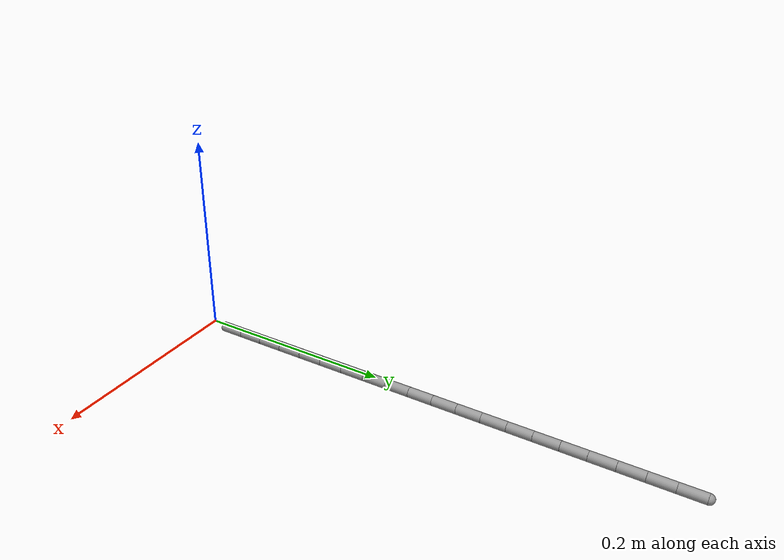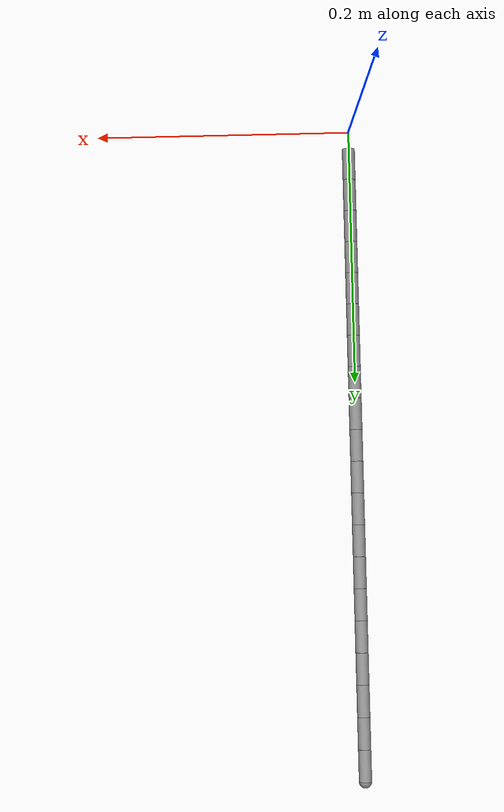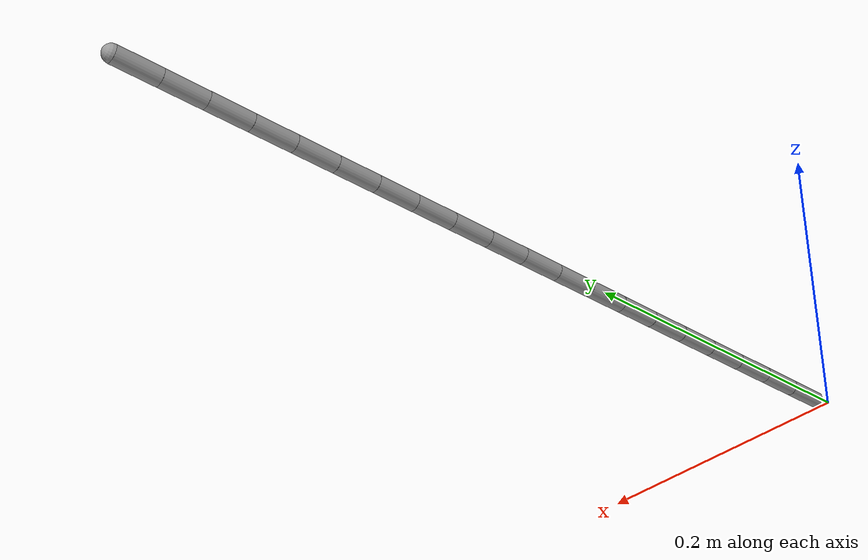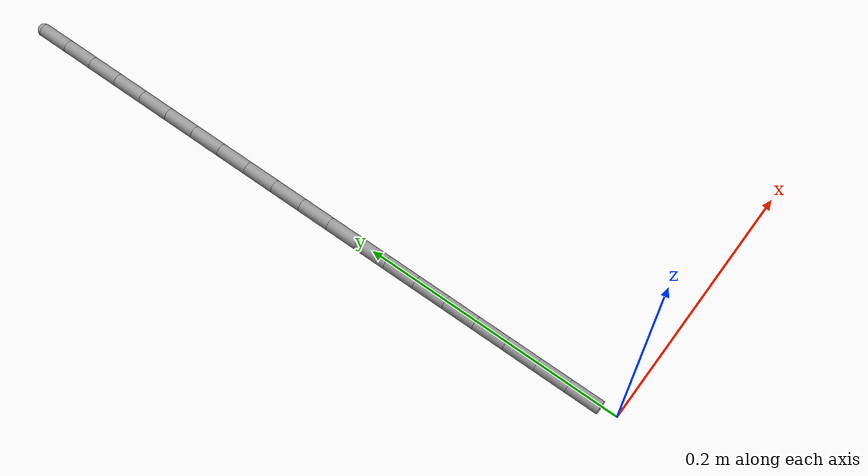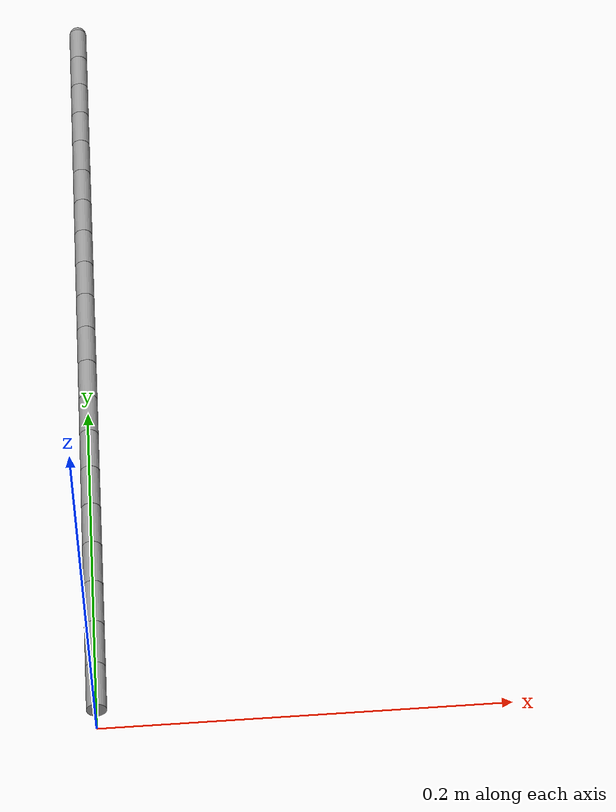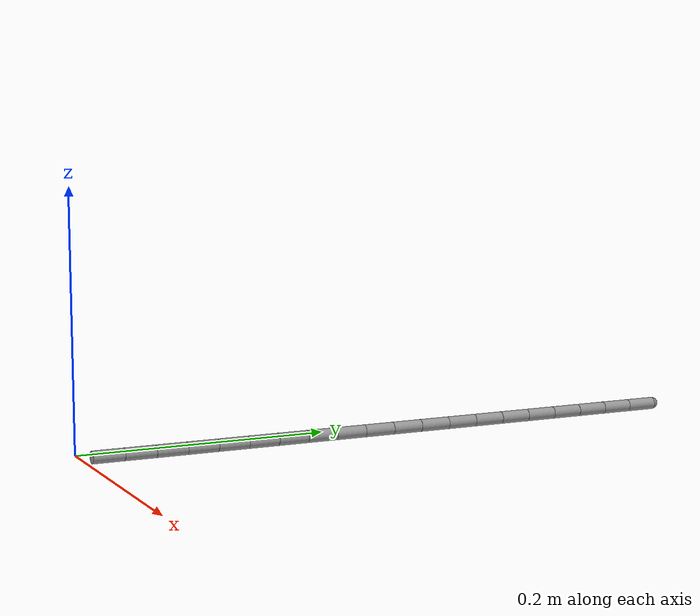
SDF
<?xml version="1.0" ?>
<sdf version='1.5'>
  <model name='cable'>

    <link name="link_1">    <!-- m = 0.1 used for plots-->
      <pose>0 0.025 -0.0025 1.5708 0 0</pose>
      <inertial>
        <mass> 0.0005 </mass>
        <inertia>
          <ixx>6.2500000000000005e-09</ixx>
          <ixy>0</ixy>
          <ixz>0</ixz>
          <iyy>6.2500000000000005e-09</iyy>
          <iyz>0</iyz>
          <izz>1.0729166666666668e-07</izz>
        </inertia>
        <pose>0 0 0 0 0 0</pose>
      </inertial>
      <self_collide>0</self_collide>
      <enable_wind>0</enable_wind>
      <kinematic>0</kinematic>
      <gravity>1</gravity>
      <visual name='visual_1'>
        <geometry>
          <cylinder>
            <radius>0.005</radius>
            <length>0.025</length>
          </cylinder>
        </geometry>
        <material>
          <script>
            <name>Gazebo/Grey</name>
            <uri>file://media/materials/scripts/gazebo.material</uri>
          </script>
          <shader type='pixel'>
            <normal_map>__default__</normal_map>
          </shader>
          <ambient>0.3 0.3 0.3 1</ambient>
          <diffuse>0.7 0.7 0.7 1</diffuse>
          <specular>0.01 0.01 0.01 1</specular>
          <emissive>0 0 0 1</emissive>
        </material>
        <pose>0 0 0 0 -0 0</pose>
        <transparency>0</transparency>
        <cast_shadows>1</cast_shadows>
      </visual>
      <visual name='sphere'>
        <geometry>
          <sphere>
            <radius>0.005</radius>
          </sphere>
        </geometry>
        <pose>0 0 -0.0125 0 0 0</pose>
        <material>
          <script>
            <name>Gazebo/Grey</name>
            <uri>file://media/materials/scripts/gazebo.material</uri>
          </script>
          <shader type='pixel'>
            <normal_map>__default__</normal_map>
          </shader>
          <ambient>0.3 0.3 0.3 1</ambient>
          <diffuse>0.7 0.7 0.7 1</diffuse>
          <specular>0.01 0.01 0.01 1</specular>
          <emissive>0 0 0 1</emissive>
        </material>
        <transparency>0</transparency>
        <cast_shadows>1</cast_shadows>
      </visual>
      <collision name='collision_1'>
        <laser_retro>0</laser_retro>
        <max_contacts>10</max_contacts>
        <pose>0 0 0 0 -0 0</pose>
        <geometry>
          <cylinder>
            <radius>0.005</radius>
            <length>0.025</length>
          </cylinder>
        </geometry>
        <surface>
          <friction>
            <ode>
              <mu>1</mu>
              <mu2>1</mu2>
              <fdir1>0 0 0</fdir1>
              <slip1>0</slip1>
              <slip2>0</slip2>
            </ode>
            <torsional>
              <coefficient>1</coefficient>
              <patch_radius>0</patch_radius>
              <surface_radius>0</surface_radius>
              <use_patch_radius>1</use_patch_radius>
              <ode>
                <slip>0</slip>
              </ode>
            </torsional>
          </friction>
          <bounce>
            <restitution_coefficient>0</restitution_coefficient>
            <threshold>1e+06</threshold>
          </bounce>
          <contact>
            <collide_bitmask>0</collide_bitmask>
            <ode>
              <soft_cfm>0</soft_cfm>
              <soft_erp>0.2</soft_erp>
              <kp>1e+13</kp>
              <kd>1</kd>
              <max_vel>0.01</max_vel>
              <min_depth>0</min_depth>
            </ode>
            <bullet>
              <split_impulse>1</split_impulse>
              <split_impulse_penetration_threshold>-0.01</split_impulse_penetration_threshold>
              <soft_cfm>0</soft_cfm>
              <soft_erp>0.2</soft_erp>
              <kp>1e+13</kp>
              <kd>1</kd>
            </bullet>
          </contact>
        </surface>
      </collision>
      </link>
    <link name="link_2">    <!-- m = 0.1 used for plots-->
      <pose>0 0.05 -0.0025 1.5708 0 0</pose>
      <inertial>
        <mass> 0.0005 </mass>
        <inertia>
          <ixx>6.2500000000000005e-09</ixx>
          <ixy>0</ixy>
          <ixz>0</ixz>
          <iyy>6.2500000000000005e-09</iyy>
          <iyz>0</iyz>
          <izz>1.0729166666666668e-07</izz>
        </inertia>
        <pose>0 0 0 0 0 0</pose>
      </inertial>
      <self_collide>0</self_collide>
      <enable_wind>0</enable_wind>
      <kinematic>0</kinematic>
      <gravity>1</gravity>
      <visual name='visual_2'>
        <geometry>
          <cylinder>
            <radius>0.005</radius>
            <length>0.025</length>
          </cylinder>
        </geometry>
        <material>
          <script>
            <name>Gazebo/Grey</name>
            <uri>file://media/materials/scripts/gazebo.material</uri>
          </script>
          <shader type='pixel'>
            <normal_map>__default__</normal_map>
          </shader>
          <ambient>0.3 0.3 0.3 1</ambient>
          <diffuse>0.7 0.7 0.7 1</diffuse>
          <specular>0.01 0.01 0.01 1</specular>
          <emissive>0 0 0 1</emissive>
        </material>
        <pose>0 0 0 0 -0 0</pose>
        <transparency>0</transparency>
        <cast_shadows>1</cast_shadows>
      </visual>
      <visual name='sphere'>
        <geometry>
          <sphere>
            <radius>0.005</radius>
          </sphere>
        </geometry>
        <pose>0 0 -0.0125 0 0 0</pose>
        <material>
          <script>
            <name>Gazebo/Grey</name>
            <uri>file://media/materials/scripts/gazebo.material</uri>
          </script>
          <shader type='pixel'>
            <normal_map>__default__</normal_map>
          </shader>
          <ambient>0.3 0.3 0.3 1</ambient>
          <diffuse>0.7 0.7 0.7 1</diffuse>
          <specular>0.01 0.01 0.01 1</specular>
          <emissive>0 0 0 1</emissive>
        </material>
        <transparency>0</transparency>
        <cast_shadows>1</cast_shadows>
      </visual>
      <collision name='collision_2'>
        <laser_retro>0</laser_retro>
        <max_contacts>10</max_contacts>
        <pose>0 0 0 0 -0 0</pose>
        <geometry>
          <cylinder>
            <radius>0.005</radius>
            <length>0.025</length>
          </cylinder>
        </geometry>
        <surface>
          <friction>
            <ode>
              <mu>1</mu>
              <mu2>1</mu2>
              <fdir1>0 0 0</fdir1>
              <slip1>0</slip1>
              <slip2>0</slip2>
            </ode>
            <torsional>
              <coefficient>1</coefficient>
              <patch_radius>0</patch_radius>
              <surface_radius>0</surface_radius>
              <use_patch_radius>1</use_patch_radius>
              <ode>
                <slip>0</slip>
              </ode>
            </torsional>
          </friction>
          <bounce>
            <restitution_coefficient>0</restitution_coefficient>
            <threshold>1e+06</threshold>
          </bounce>
          <contact>
            <collide_bitmask>0</collide_bitmask>
            <ode>
              <soft_cfm>0</soft_cfm>
              <soft_erp>0.2</soft_erp>
              <kp>1e+13</kp>
              <kd>1</kd>
              <max_vel>0.01</max_vel>
              <min_depth>0</min_depth>
            </ode>
            <bullet>
              <split_impulse>1</split_impulse>
              <split_impulse_penetration_threshold>-0.01</split_impulse_penetration_threshold>
              <soft_cfm>0</soft_cfm>
              <soft_erp>0.2</soft_erp>
              <kp>1e+13</kp>
              <kd>1</kd>
            </bullet>
          </contact>
        </surface>
      </collision>
      </link>
    <link name="link_3">    <!-- m = 0.1 used for plots-->
      <pose>0 0.07500000000000001 -0.0025 1.5708 0 0</pose>
      <inertial>
        <mass> 0.0005 </mass>
        <inertia>
          <ixx>6.2500000000000005e-09</ixx>
          <ixy>0</ixy>
          <ixz>0</ixz>
          <iyy>6.2500000000000005e-09</iyy>
          <iyz>0</iyz>
          <izz>1.0729166666666668e-07</izz>
        </inertia>
        <pose>0 0 0 0 0 0</pose>
      </inertial>
      <self_collide>0</self_collide>
      <enable_wind>0</enable_wind>
      <kinematic>0</kinematic>
      <gravity>1</gravity>
      <visual name='visual_3'>
        <geometry>
          <cylinder>
            <radius>0.005</radius>
            <length>0.025</length>
          </cylinder>
        </geometry>
        <material>
          <script>
            <name>Gazebo/Grey</name>
            <uri>file://media/materials/scripts/gazebo.material</uri>
          </script>
          <shader type='pixel'>
            <normal_map>__default__</normal_map>
          </shader>
          <ambient>0.3 0.3 0.3 1</ambient>
          <diffuse>0.7 0.7 0.7 1</diffuse>
          <specular>0.01 0.01 0.01 1</specular>
          <emissive>0 0 0 1</emissive>
        </material>
        <pose>0 0 0 0 -0 0</pose>
        <transparency>0</transparency>
        <cast_shadows>1</cast_shadows>
      </visual>
      <visual name='sphere'>
        <geometry>
          <sphere>
            <radius>0.005</radius>
          </sphere>
        </geometry>
        <pose>0 0 -0.0125 0 0 0</pose>
        <material>
          <script>
            <name>Gazebo/Grey</name>
            <uri>file://media/materials/scripts/gazebo.material</uri>
          </script>
          <shader type='pixel'>
            <normal_map>__default__</normal_map>
          </shader>
          <ambient>0.3 0.3 0.3 1</ambient>
          <diffuse>0.7 0.7 0.7 1</diffuse>
          <specular>0.01 0.01 0.01 1</specular>
          <emissive>0 0 0 1</emissive>
        </material>
        <transparency>0</transparency>
        <cast_shadows>1</cast_shadows>
      </visual>
      <collision name='collision_3'>
        <laser_retro>0</laser_retro>
        <max_contacts>10</max_contacts>
        <pose>0 0 0 0 -0 0</pose>
        <geometry>
          <cylinder>
            <radius>0.005</radius>
            <length>0.025</length>
          </cylinder>
        </geometry>
        <surface>
          <friction>
            <ode>
              <mu>1</mu>
              <mu2>1</mu2>
              <fdir1>0 0 0</fdir1>
              <slip1>0</slip1>
              <slip2>0</slip2>
            </ode>
            <torsional>
              <coefficient>1</coefficient>
              <patch_radius>0</patch_radius>
              <surface_radius>0</surface_radius>
              <use_patch_radius>1</use_patch_radius>
              <ode>
                <slip>0</slip>
              </ode>
            </torsional>
          </friction>
          <bounce>
            <restitution_coefficient>0</restitution_coefficient>
            <threshold>1e+06</threshold>
          </bounce>
          <contact>
            <collide_bitmask>0</collide_bitmask>
            <ode>
              <soft_cfm>0</soft_cfm>
              <soft_erp>0.2</soft_erp>
              <kp>1e+13</kp>
              <kd>1</kd>
              <max_vel>0.01</max_vel>
              <min_depth>0</min_depth>
            </ode>
            <bullet>
              <split_impulse>1</split_impulse>
              <split_impulse_penetration_threshold>-0.01</split_impulse_penetration_threshold>
              <soft_cfm>0</soft_cfm>
              <soft_erp>0.2</soft_erp>
              <kp>1e+13</kp>
              <kd>1</kd>
            </bullet>
          </contact>
        </surface>
      </collision>
      </link>
    <link name="link_4">    <!-- m = 0.1 used for plots-->
      <pose>0 0.1 -0.0025 1.5708 0 0</pose>
      <inertial>
        <mass> 0.0005 </mass>
        <inertia>
          <ixx>6.2500000000000005e-09</ixx>
          <ixy>0</ixy>
          <ixz>0</ixz>
          <iyy>6.2500000000000005e-09</iyy>
          <iyz>0</iyz>
          <izz>1.0729166666666668e-07</izz>
        </inertia>
        <pose>0 0 0 0 0 0</pose>
      </inertial>
      <self_collide>0</self_collide>
      <enable_wind>0</enable_wind>
      <kinematic>0</kinematic>
      <gravity>1</gravity>
      <visual name='visual_4'>
        <geometry>
          <cylinder>
            <radius>0.005</radius>
            <length>0.025</length>
          </cylinder>
        </geometry>
        <material>
          <script>
            <name>Gazebo/Grey</name>
            <uri>file://media/materials/scripts/gazebo.material</uri>
          </script>
          <shader type='pixel'>
            <normal_map>__default__</normal_map>
          </shader>
          <ambient>0.3 0.3 0.3 1</ambient>
          <diffuse>0.7 0.7 0.7 1</diffuse>
          <specular>0.01 0.01 0.01 1</specular>
          <emissive>0 0 0 1</emissive>
        </material>
        <pose>0 0 0 0 -0 0</pose>
        <transparency>0</transparency>
        <cast_shadows>1</cast_shadows>
      </visual>
      <visual name='sphere'>
        <geometry>
          <sphere>
            <radius>0.005</radius>
          </sphere>
        </geometry>
        <pose>0 0 -0.0125 0 0 0</pose>
        <material>
          <script>
            <name>Gazebo/Grey</name>
            <uri>file://media/materials/scripts/gazebo.material</uri>
          </script>
          <shader type='pixel'>
            <normal_map>__default__</normal_map>
          </shader>
          <ambient>0.3 0.3 0.3 1</ambient>
          <diffuse>0.7 0.7 0.7 1</diffuse>
          <specular>0.01 0.01 0.01 1</specular>
          <emissive>0 0 0 1</emissive>
        </material>
        <transparency>0</transparency>
        <cast_shadows>1</cast_shadows>
      </visual>
      <collision name='collision_4'>
        <laser_retro>0</laser_retro>
        <max_contacts>10</max_contacts>
        <pose>0 0 0 0 -0 0</pose>
        <geometry>
          <cylinder>
            <radius>0.005</radius>
            <length>0.025</length>
          </cylinder>
        </geometry>
        <surface>
          <friction>
            <ode>
              <mu>1</mu>
              <mu2>1</mu2>
              <fdir1>0 0 0</fdir1>
              <slip1>0</slip1>
              <slip2>0</slip2>
            </ode>
            <torsional>
              <coefficient>1</coefficient>
              <patch_radius>0</patch_radius>
              <surface_radius>0</surface_radius>
              <use_patch_radius>1</use_patch_radius>
              <ode>
                <slip>0</slip>
              </ode>
            </torsional>
          </friction>
          <bounce>
            <restitution_coefficient>0</restitution_coefficient>
            <threshold>1e+06</threshold>
          </bounce>
          <contact>
            <collide_bitmask>0</collide_bitmask>
            <ode>
              <soft_cfm>0</soft_cfm>
              <soft_erp>0.2</soft_erp>
              <kp>1e+13</kp>
              <kd>1</kd>
              <max_vel>0.01</max_vel>
              <min_depth>0</min_depth>
            </ode>
            <bullet>
              <split_impulse>1</split_impulse>
              <split_impulse_penetration_threshold>-0.01</split_impulse_penetration_threshold>
              <soft_cfm>0</soft_cfm>
              <soft_erp>0.2</soft_erp>
              <kp>1e+13</kp>
              <kd>1</kd>
            </bullet>
          </contact>
        </surface>
      </collision>
      </link>
    <link name="link_5">    <!-- m = 0.1 used for plots-->
      <pose>0 0.125 -0.0025 1.5708 0 0</pose>
      <inertial>
        <mass> 0.0005 </mass>
        <inertia>
          <ixx>6.2500000000000005e-09</ixx>
          <ixy>0</ixy>
          <ixz>0</ixz>
          <iyy>6.2500000000000005e-09</iyy>
          <iyz>0</iyz>
          <izz>1.0729166666666668e-07</izz>
        </inertia>
        <pose>0 0 0 0 0 0</pose>
      </inertial>
      <self_collide>0</self_collide>
      <enable_wind>0</enable_wind>
      <kinematic>0</kinematic>
      <gravity>1</gravity>
      <visual name='visual_5'>
        <geometry>
          <cylinder>
            <radius>0.005</radius>
            <length>0.025</length>
          </cylinder>
        </geometry>
        <material>
          <script>
            <name>Gazebo/Grey</name>
            <uri>file://media/materials/scripts/gazebo.material</uri>
          </script>
          <shader type='pixel'>
            <normal_map>__default__</normal_map>
          </shader>
          <ambient>0.3 0.3 0.3 1</ambient>
          <diffuse>0.7 0.7 0.7 1</diffuse>
          <specular>0.01 0.01 0.01 1</specular>
          <emissive>0 0 0 1</emissive>
        </material>
        <pose>0 0 0 0 -0 0</pose>
        <transparency>0</transparency>
        <cast_shadows>1</cast_shadows>
      </visual>
      <visual name='sphere'>
        <geometry>
          <sphere>
            <radius>0.005</radius>
          </sphere>
        </geometry>
        <pose>0 0 -0.0125 0 0 0</pose>
        <material>
          <script>
            <name>Gazebo/Grey</name>
            <uri>file://media/materials/scripts/gazebo.material</uri>
          </script>
          <shader type='pixel'>
            <normal_map>__default__</normal_map>
          </shader>
          <ambient>0.3 0.3 0.3 1</ambient>
          <diffuse>0.7 0.7 0.7 1</diffuse>
          <specular>0.01 0.01 0.01 1</specular>
          <emissive>0 0 0 1</emissive>
        </material>
        <transparency>0</transparency>
        <cast_shadows>1</cast_shadows>
      </visual>
      <collision name='collision_5'>
        <laser_retro>0</laser_retro>
        <max_contacts>10</max_contacts>
        <pose>0 0 0 0 -0 0</pose>
        <geometry>
          <cylinder>
            <radius>0.005</radius>
            <length>0.025</length>
          </cylinder>
        </geometry>
        <surface>
          <friction>
            <ode>
              <mu>1</mu>
              <mu2>1</mu2>
              <fdir1>0 0 0</fdir1>
              <slip1>0</slip1>
              <slip2>0</slip2>
            </ode>
            <torsional>
              <coefficient>1</coefficient>
              <patch_radius>0</patch_radius>
              <surface_radius>0</surface_radius>
              <use_patch_radius>1</use_patch_radius>
              <ode>
                <slip>0</slip>
              </ode>
            </torsional>
          </friction>
          <bounce>
            <restitution_coefficient>0</restitution_coefficient>
            <threshold>1e+06</threshold>
          </bounce>
          <contact>
            <collide_bitmask>0</collide_bitmask>
            <ode>
              <soft_cfm>0</soft_cfm>
              <soft_erp>0.2</soft_erp>
              <kp>1e+13</kp>
              <kd>1</kd>
              <max_vel>0.01</max_vel>
              <min_depth>0</min_depth>
            </ode>
            <bullet>
              <split_impulse>1</split_impulse>
              <split_impulse_penetration_threshold>-0.01</split_impulse_penetration_threshold>
              <soft_cfm>0</soft_cfm>
              <soft_erp>0.2</soft_erp>
              <kp>1e+13</kp>
              <kd>1</kd>
            </bullet>
          </contact>
        </surface>
      </collision>
      </link>
    <link name="link_6">    <!-- m = 0.1 used for plots-->
      <pose>0 0.15000000000000002 -0.0025 1.5708 0 0</pose>
      <inertial>
        <mass> 0.0005 </mass>
        <inertia>
          <ixx>6.2500000000000005e-09</ixx>
          <ixy>0</ixy>
          <ixz>0</ixz>
          <iyy>6.2500000000000005e-09</iyy>
          <iyz>0</iyz>
          <izz>1.0729166666666668e-07</izz>
        </inertia>
        <pose>0 0 0 0 0 0</pose>
      </inertial>
      <self_collide>0</self_collide>
      <enable_wind>0</enable_wind>
      <kinematic>0</kinematic>
      <gravity>1</gravity>
      <visual name='visual_6'>
        <geometry>
          <cylinder>
            <radius>0.005</radius>
            <length>0.025</length>
          </cylinder>
        </geometry>
        <material>
          <script>
            <name>Gazebo/Grey</name>
            <uri>file://media/materials/scripts/gazebo.material</uri>
          </script>
          <shader type='pixel'>
            <normal_map>__default__</normal_map>
          </shader>
          <ambient>0.3 0.3 0.3 1</ambient>
          <diffuse>0.7 0.7 0.7 1</diffuse>
          <specular>0.01 0.01 0.01 1</specular>
          <emissive>0 0 0 1</emissive>
        </material>
        <pose>0 0 0 0 -0 0</pose>
        <transparency>0</transparency>
        <cast_shadows>1</cast_shadows>
      </visual>
      <visual name='sphere'>
        <geometry>
          <sphere>
            <radius>0.005</radius>
          </sphere>
        </geometry>
        <pose>0 0 -0.0125 0 0 0</pose>
        <material>
          <script>
            <name>Gazebo/Grey</name>
            <uri>file://media/materials/scripts/gazebo.material</uri>
          </script>
          <shader type='pixel'>
            <normal_map>__default__</normal_map>
          </shader>
          <ambient>0.3 0.3 0.3 1</ambient>
          <diffuse>0.7 0.7 0.7 1</diffuse>
          <specular>0.01 0.01 0.01 1</specular>
          <emissive>0 0 0 1</emissive>
        </material>
        <transparency>0</transparency>
        <cast_shadows>1</cast_shadows>
      </visual>
      <collision name='collision_6'>
        <laser_retro>0</laser_retro>
        <max_contacts>10</max_contacts>
        <pose>0 0 0 0 -0 0</pose>
        <geometry>
          <cylinder>
            <radius>0.005</radius>
            <length>0.025</length>
          </cylinder>
        </geometry>
        <surface>
          <friction>
            <ode>
              <mu>1</mu>
              <mu2>1</mu2>
              <fdir1>0 0 0</fdir1>
              <slip1>0</slip1>
              <slip2>0</slip2>
            </ode>
            <torsional>
              <coefficient>1</coefficient>
              <patch_radius>0</patch_radius>
              <surface_radius>0</surface_radius>
              <use_patch_radius>1</use_patch_radius>
              <ode>
                <slip>0</slip>
              </ode>
            </torsional>
          </friction>
          <bounce>
            <restitution_coefficient>0</restitution_coefficient>
            <threshold>1e+06</threshold>
          </bounce>
          <contact>
            <collide_bitmask>0</collide_bitmask>
            <ode>
              <soft_cfm>0</soft_cfm>
              <soft_erp>0.2</soft_erp>
              <kp>1e+13</kp>
              <kd>1</kd>
              <max_vel>0.01</max_vel>
              <min_depth>0</min_depth>
            </ode>
            <bullet>
              <split_impulse>1</split_impulse>
              <split_impulse_penetration_threshold>-0.01</split_impulse_penetration_threshold>
              <soft_cfm>0</soft_cfm>
              <soft_erp>0.2</soft_erp>
              <kp>1e+13</kp>
              <kd>1</kd>
            </bullet>
          </contact>
        </surface>
      </collision>
      </link>
    <link name="link_7">    <!-- m = 0.1 used for plots-->
      <pose>0 0.17500000000000002 -0.0025 1.5708 0 0</pose>
      <inertial>
        <mass> 0.0005 </mass>
        <inertia>
          <ixx>6.2500000000000005e-09</ixx>
          <ixy>0</ixy>
          <ixz>0</ixz>
          <iyy>6.2500000000000005e-09</iyy>
          <iyz>0</iyz>
          <izz>1.0729166666666668e-07</izz>
        </inertia>
        <pose>0 0 0 0 0 0</pose>
      </inertial>
      <self_collide>0</self_collide>
      <enable_wind>0</enable_wind>
      <kinematic>0</kinematic>
      <gravity>1</gravity>
      <visual name='visual_7'>
        <geometry>
          <cylinder>
            <radius>0.005</radius>
            <length>0.025</length>
          </cylinder>
        </geometry>
        <material>
          <script>
            <name>Gazebo/Grey</name>
            <uri>file://media/materials/scripts/gazebo.material</uri>
          </script>
          <shader type='pixel'>
            <normal_map>__default__</normal_map>
          </shader>
          <ambient>0.3 0.3 0.3 1</ambient>
          <diffuse>0.7 0.7 0.7 1</diffuse>
          <specular>0.01 0.01 0.01 1</specular>
          <emissive>0 0 0 1</emissive>
        </material>
        <pose>0 0 0 0 -0 0</pose>
        <transparency>0</transparency>
        <cast_shadows>1</cast_shadows>
      </visual>
      <visual name='sphere'>
        <geometry>
          <sphere>
            <radius>0.005</radius>
          </sphere>
        </geometry>
        <pose>0 0 -0.0125 0 0 0</pose>
        <material>
          <script>
            <name>Gazebo/Grey</name>
            <uri>file://media/materials/scripts/gazebo.material</uri>
          </script>
          <shader type='pixel'>
            <normal_map>__default__</normal_map>
          </shader>
          <ambient>0.3 0.3 0.3 1</ambient>
          <diffuse>0.7 0.7 0.7 1</diffuse>
          <specular>0.01 0.01 0.01 1</specular>
          <emissive>0 0 0 1</emissive>
        </material>
        <transparency>0</transparency>
        <cast_shadows>1</cast_shadows>
      </visual>
      <collision name='collision_7'>
        <laser_retro>0</laser_retro>
        <max_contacts>10</max_contacts>
        <pose>0 0 0 0 -0 0</pose>
        <geometry>
          <cylinder>
            <radius>0.005</radius>
            <length>0.025</length>
          </cylinder>
        </geometry>
        <surface>
          <friction>
            <ode>
              <mu>1</mu>
              <mu2>1</mu2>
              <fdir1>0 0 0</fdir1>
              <slip1>0</slip1>
              <slip2>0</slip2>
            </ode>
            <torsional>
              <coefficient>1</coefficient>
              <patch_radius>0</patch_radius>
              <surface_radius>0</surface_radius>
              <use_patch_radius>1</use_patch_radius>
              <ode>
                <slip>0</slip>
              </ode>
            </torsional>
          </friction>
          <bounce>
            <restitution_coefficient>0</restitution_coefficient>
            <threshold>1e+06</threshold>
          </bounce>
          <contact>
            <collide_bitmask>0</collide_bitmask>
            <ode>
              <soft_cfm>0</soft_cfm>
              <soft_erp>0.2</soft_erp>
              <kp>1e+13</kp>
              <kd>1</kd>
              <max_vel>0.01</max_vel>
              <min_depth>0</min_depth>
            </ode>
            <bullet>
              <split_impulse>1</split_impulse>
              <split_impulse_penetration_threshold>-0.01</split_impulse_penetration_threshold>
              <soft_cfm>0</soft_cfm>
              <soft_erp>0.2</soft_erp>
              <kp>1e+13</kp>
              <kd>1</kd>
            </bullet>
          </contact>
        </surface>
      </collision>
      </link>
    <link name="link_8">    <!-- m = 0.1 used for plots-->
      <pose>0 0.2 -0.0025 1.5708 0 0</pose>
      <inertial>
        <mass> 0.0005 </mass>
        <inertia>
          <ixx>6.2500000000000005e-09</ixx>
          <ixy>0</ixy>
          <ixz>0</ixz>
          <iyy>6.2500000000000005e-09</iyy>
          <iyz>0</iyz>
          <izz>1.0729166666666668e-07</izz>
        </inertia>
        <pose>0 0 0 0 0 0</pose>
      </inertial>
      <self_collide>0</self_collide>
      <enable_wind>0</enable_wind>
      <kinematic>0</kinematic>
      <gravity>1</gravity>
      <visual name='visual_8'>
        <geometry>
          <cylinder>
            <radius>0.005</radius>
            <length>0.025</length>
          </cylinder>
        </geometry>
        <material>
          <script>
            <name>Gazebo/Grey</name>
            <uri>file://media/materials/scripts/gazebo.material</uri>
          </script>
          <shader type='pixel'>
            <normal_map>__default__</normal_map>
          </shader>
          <ambient>0.3 0.3 0.3 1</ambient>
          <diffuse>0.7 0.7 0.7 1</diffuse>
          <specular>0.01 0.01 0.01 1</specular>
          <emissive>0 0 0 1</emissive>
        </material>
        <pose>0 0 0 0 -0 0</pose>
        <transparency>0</transparency>
        <cast_shadows>1</cast_shadows>
      </visual>
      <visual name='sphere'>
        <geometry>
          <sphere>
            <radius>0.005</radius>
          </sphere>
        </geometry>
        <pose>0 0 -0.0125 0 0 0</pose>
        <material>
          <script>
            <name>Gazebo/Grey</name>
            <uri>file://media/materials/scripts/gazebo.material</uri>
          </script>
          <shader type='pixel'>
            <normal_map>__default__</normal_map>
          </shader>
          <ambient>0.3 0.3 0.3 1</ambient>
          <diffuse>0.7 0.7 0.7 1</diffuse>
          <specular>0.01 0.01 0.01 1</specular>
          <emissive>0 0 0 1</emissive>
        </material>
        <transparency>0</transparency>
        <cast_shadows>1</cast_shadows>
      </visual>
      <collision name='collision_8'>
        <laser_retro>0</laser_retro>
        <max_contacts>10</max_contacts>
        <pose>0 0 0 0 -0 0</pose>
        <geometry>
          <cylinder>
            <radius>0.005</radius>
            <length>0.025</length>
          </cylinder>
        </geometry>
        <surface>
          <friction>
            <ode>
              <mu>1</mu>
              <mu2>1</mu2>
              <fdir1>0 0 0</fdir1>
              <slip1>0</slip1>
              <slip2>0</slip2>
            </ode>
            <torsional>
              <coefficient>1</coefficient>
              <patch_radius>0</patch_radius>
              <surface_radius>0</surface_radius>
              <use_patch_radius>1</use_patch_radius>
              <ode>
                <slip>0</slip>
              </ode>
            </torsional>
          </friction>
          <bounce>
            <restitution_coefficient>0</restitution_coefficient>
            <threshold>1e+06</threshold>
          </bounce>
          <contact>
            <collide_bitmask>0</collide_bitmask>
            <ode>
              <soft_cfm>0</soft_cfm>
              <soft_erp>0.2</soft_erp>
              <kp>1e+13</kp>
              <kd>1</kd>
              <max_vel>0.01</max_vel>
              <min_depth>0</min_depth>
            </ode>
            <bullet>
              <split_impulse>1</split_impulse>
              <split_impulse_penetration_threshold>-0.01</split_impulse_penetration_threshold>
              <soft_cfm>0</soft_cfm>
              <soft_erp>0.2</soft_erp>
              <kp>1e+13</kp>
              <kd>1</kd>
            </bullet>
          </contact>
        </surface>
      </collision>
      </link>
    <link name="link_9">    <!-- m = 0.1 used for plots-->
      <pose>0 0.225 -0.0025 1.5708 0 0</pose>
      <inertial>
        <mass> 0.0005 </mass>
        <inertia>
          <ixx>6.2500000000000005e-09</ixx>
          <ixy>0</ixy>
          <ixz>0</ixz>
          <iyy>6.2500000000000005e-09</iyy>
          <iyz>0</iyz>
          <izz>1.0729166666666668e-07</izz>
        </inertia>
        <pose>0 0 0 0 0 0</pose>
      </inertial>
      <self_collide>0</self_collide>
      <enable_wind>0</enable_wind>
      <kinematic>0</kinematic>
      <gravity>1</gravity>
      <visual name='visual_9'>
        <geometry>
          <cylinder>
            <radius>0.005</radius>
            <length>0.025</length>
          </cylinder>
        </geometry>
        <material>
          <script>
            <name>Gazebo/Grey</name>
            <uri>file://media/materials/scripts/gazebo.material</uri>
          </script>
          <shader type='pixel'>
            <normal_map>__default__</normal_map>
          </shader>
          <ambient>0.3 0.3 0.3 1</ambient>
          <diffuse>0.7 0.7 0.7 1</diffuse>
          <specular>0.01 0.01 0.01 1</specular>
          <emissive>0 0 0 1</emissive>
        </material>
        <pose>0 0 0 0 -0 0</pose>
        <transparency>0</transparency>
        <cast_shadows>1</cast_shadows>
      </visual>
      <visual name='sphere'>
        <geometry>
          <sphere>
            <radius>0.005</radius>
          </sphere>
        </geometry>
        <pose>0 0 -0.0125 0 0 0</pose>
        <material>
          <script>
            <name>Gazebo/Grey</name>
            <uri>file://media/materials/scripts/gazebo.material</uri>
          </script>
          <shader type='pixel'>
            <normal_map>__default__</normal_map>
          </shader>
          <ambient>0.3 0.3 0.3 1</ambient>
          <diffuse>0.7 0.7 0.7 1</diffuse>
          <specular>0.01 0.01 0.01 1</specular>
          <emissive>0 0 0 1</emissive>
        </material>
        <transparency>0</transparency>
        <cast_shadows>1</cast_shadows>
      </visual>
      <collision name='collision_9'>
        <laser_retro>0</laser_retro>
        <max_contacts>10</max_contacts>
        <pose>0 0 0 0 -0 0</pose>
        <geometry>
          <cylinder>
            <radius>0.005</radius>
            <length>0.025</length>
          </cylinder>
        </geometry>
        <surface>
          <friction>
            <ode>
              <mu>1</mu>
              <mu2>1</mu2>
              <fdir1>0 0 0</fdir1>
              <slip1>0</slip1>
              <slip2>0</slip2>
            </ode>
            <torsional>
              <coefficient>1</coefficient>
              <patch_radius>0</patch_radius>
              <surface_radius>0</surface_radius>
              <use_patch_radius>1</use_patch_radius>
              <ode>
                <slip>0</slip>
              </ode>
            </torsional>
          </friction>
          <bounce>
            <restitution_coefficient>0</restitution_coefficient>
            <threshold>1e+06</threshold>
          </bounce>
          <contact>
            <collide_bitmask>0</collide_bitmask>
            <ode>
              <soft_cfm>0</soft_cfm>
              <soft_erp>0.2</soft_erp>
              <kp>1e+13</kp>
              <kd>1</kd>
              <max_vel>0.01</max_vel>
              <min_depth>0</min_depth>
            </ode>
            <bullet>
              <split_impulse>1</split_impulse>
              <split_impulse_penetration_threshold>-0.01</split_impulse_penetration_threshold>
              <soft_cfm>0</soft_cfm>
              <soft_erp>0.2</soft_erp>
              <kp>1e+13</kp>
              <kd>1</kd>
            </bullet>
          </contact>
        </surface>
      </collision>
      </link>
    <link name="link_10">    <!-- m = 0.1 used for plots-->
      <pose>0 0.25 -0.0025 1.5708 0 0</pose>
      <inertial>
        <mass> 0.0005 </mass>
        <inertia>
          <ixx>6.2500000000000005e-09</ixx>
          <ixy>0</ixy>
          <ixz>0</ixz>
          <iyy>6.2500000000000005e-09</iyy>
          <iyz>0</iyz>
          <izz>1.0729166666666668e-07</izz>
        </inertia>
        <pose>0 0 0 0 0 0</pose>
      </inertial>
      <self_collide>0</self_collide>
      <enable_wind>0</enable_wind>
      <kinematic>0</kinematic>
      <gravity>1</gravity>
      <visual name='visual_10'>
        <geometry>
          <cylinder>
            <radius>0.005</radius>
            <length>0.025</length>
          </cylinder>
        </geometry>
        <material>
          <script>
            <name>Gazebo/Grey</name>
            <uri>file://media/materials/scripts/gazebo.material</uri>
          </script>
          <shader type='pixel'>
            <normal_map>__default__</normal_map>
          </shader>
          <ambient>0.3 0.3 0.3 1</ambient>
          <diffuse>0.7 0.7 0.7 1</diffuse>
          <specular>0.01 0.01 0.01 1</specular>
          <emissive>0 0 0 1</emissive>
        </material>
        <pose>0 0 0 0 -0 0</pose>
        <transparency>0</transparency>
        <cast_shadows>1</cast_shadows>
      </visual>
      <visual name='sphere'>
        <geometry>
          <sphere>
            <radius>0.005</radius>
          </sphere>
        </geometry>
        <pose>0 0 -0.0125 0 0 0</pose>
        <material>
          <script>
            <name>Gazebo/Grey</name>
            <uri>file://media/materials/scripts/gazebo.material</uri>
          </script>
          <shader type='pixel'>
            <normal_map>__default__</normal_map>
          </shader>
          <ambient>0.3 0.3 0.3 1</ambient>
          <diffuse>0.7 0.7 0.7 1</diffuse>
          <specular>0.01 0.01 0.01 1</specular>
          <emissive>0 0 0 1</emissive>
        </material>
        <transparency>0</transparency>
        <cast_shadows>1</cast_shadows>
      </visual>
      <collision name='collision_10'>
        <laser_retro>0</laser_retro>
        <max_contacts>10</max_contacts>
        <pose>0 0 0 0 -0 0</pose>
        <geometry>
          <cylinder>
            <radius>0.005</radius>
            <length>0.025</length>
          </cylinder>
        </geometry>
        <surface>
          <friction>
            <ode>
              <mu>1</mu>
              <mu2>1</mu2>
              <fdir1>0 0 0</fdir1>
              <slip1>0</slip1>
              <slip2>0</slip2>
            </ode>
            <torsional>
              <coefficient>1</coefficient>
              <patch_radius>0</patch_radius>
              <surface_radius>0</surface_radius>
              <use_patch_radius>1</use_patch_radius>
              <ode>
                <slip>0</slip>
              </ode>
            </torsional>
          </friction>
          <bounce>
            <restitution_coefficient>0</restitution_coefficient>
            <threshold>1e+06</threshold>
          </bounce>
          <contact>
            <collide_bitmask>0</collide_bitmask>
            <ode>
              <soft_cfm>0</soft_cfm>
              <soft_erp>0.2</soft_erp>
              <kp>1e+13</kp>
              <kd>1</kd>
              <max_vel>0.01</max_vel>
              <min_depth>0</min_depth>
            </ode>
            <bullet>
              <split_impulse>1</split_impulse>
              <split_impulse_penetration_threshold>-0.01</split_impulse_penetration_threshold>
              <soft_cfm>0</soft_cfm>
              <soft_erp>0.2</soft_erp>
              <kp>1e+13</kp>
              <kd>1</kd>
            </bullet>
          </contact>
        </surface>
      </collision>
      </link>
    <link name="link_11">    <!-- m = 0.1 used for plots-->
      <pose>0 0.275 -0.0025 1.5708 0 0</pose>
      <inertial>
        <mass> 0.0005 </mass>
        <inertia>
          <ixx>6.2500000000000005e-09</ixx>
          <ixy>0</ixy>
          <ixz>0</ixz>
          <iyy>6.2500000000000005e-09</iyy>
          <iyz>0</iyz>
          <izz>1.0729166666666668e-07</izz>
        </inertia>
        <pose>0 0 0 0 0 0</pose>
      </inertial>
      <self_collide>0</self_collide>
      <enable_wind>0</enable_wind>
      <kinematic>0</kinematic>
      <gravity>1</gravity>
      <visual name='visual_11'>
        <geometry>
          <cylinder>
            <radius>0.005</radius>
            <length>0.025</length>
          </cylinder>
        </geometry>
        <material>
          <script>
            <name>Gazebo/Grey</name>
            <uri>file://media/materials/scripts/gazebo.material</uri>
          </script>
          <shader type='pixel'>
            <normal_map>__default__</normal_map>
          </shader>
          <ambient>0.3 0.3 0.3 1</ambient>
          <diffuse>0.7 0.7 0.7 1</diffuse>
          <specular>0.01 0.01 0.01 1</specular>
          <emissive>0 0 0 1</emissive>
        </material>
        <pose>0 0 0 0 -0 0</pose>
        <transparency>0</transparency>
        <cast_shadows>1</cast_shadows>
      </visual>
      <visual name='sphere'>
        <geometry>
          <sphere>
            <radius>0.005</radius>
          </sphere>
        </geometry>
        <pose>0 0 -0.0125 0 0 0</pose>
        <material>
          <script>
            <name>Gazebo/Grey</name>
            <uri>file://media/materials/scripts/gazebo.material</uri>
          </script>
          <shader type='pixel'>
            <normal_map>__default__</normal_map>
          </shader>
          <ambient>0.3 0.3 0.3 1</ambient>
          <diffuse>0.7 0.7 0.7 1</diffuse>
          <specular>0.01 0.01 0.01 1</specular>
          <emissive>0 0 0 1</emissive>
        </material>
        <transparency>0</transparency>
        <cast_shadows>1</cast_shadows>
      </visual>
      <collision name='collision_11'>
        <laser_retro>0</laser_retro>
        <max_contacts>10</max_contacts>
        <pose>0 0 0 0 -0 0</pose>
        <geometry>
          <cylinder>
            <radius>0.005</radius>
            <length>0.025</length>
          </cylinder>
        </geometry>
        <surface>
          <friction>
            <ode>
              <mu>1</mu>
              <mu2>1</mu2>
              <fdir1>0 0 0</fdir1>
              <slip1>0</slip1>
              <slip2>0</slip2>
            </ode>
            <torsional>
              <coefficient>1</coefficient>
              <patch_radius>0</patch_radius>
              <surface_radius>0</surface_radius>
              <use_patch_radius>1</use_patch_radius>
              <ode>
                <slip>0</slip>
              </ode>
            </torsional>
          </friction>
          <bounce>
            <restitution_coefficient>0</restitution_coefficient>
            <threshold>1e+06</threshold>
          </bounce>
          <contact>
            <collide_bitmask>0</collide_bitmask>
            <ode>
              <soft_cfm>0</soft_cfm>
              <soft_erp>0.2</soft_erp>
              <kp>1e+13</kp>
              <kd>1</kd>
              <max_vel>0.01</max_vel>
              <min_depth>0</min_depth>
            </ode>
            <bullet>
              <split_impulse>1</split_impulse>
              <split_impulse_penetration_threshold>-0.01</split_impulse_penetration_threshold>
              <soft_cfm>0</soft_cfm>
              <soft_erp>0.2</soft_erp>
              <kp>1e+13</kp>
              <kd>1</kd>
            </bullet>
          </contact>
        </surface>
      </collision>
      </link>
    <link name="link_12">    <!-- m = 0.1 used for plots-->
      <pose>0 0.30000000000000004 -0.0025 1.5708 0 0</pose>
      <inertial>
        <mass> 0.0005 </mass>
        <inertia>
          <ixx>6.2500000000000005e-09</ixx>
          <ixy>0</ixy>
          <ixz>0</ixz>
          <iyy>6.2500000000000005e-09</iyy>
          <iyz>0</iyz>
          <izz>1.0729166666666668e-07</izz>
        </inertia>
        <pose>0 0 0 0 0 0</pose>
      </inertial>
      <self_collide>0</self_collide>
      <enable_wind>0</enable_wind>
      <kinematic>0</kinematic>
      <gravity>1</gravity>
      <visual name='visual_12'>
        <geometry>
          <cylinder>
            <radius>0.005</radius>
            <length>0.025</length>
          </cylinder>
        </geometry>
        <material>
          <script>
            <name>Gazebo/Grey</name>
            <uri>file://media/materials/scripts/gazebo.material</uri>
          </script>
          <shader type='pixel'>
            <normal_map>__default__</normal_map>
          </shader>
          <ambient>0.3 0.3 0.3 1</ambient>
          <diffuse>0.7 0.7 0.7 1</diffuse>
          <specular>0.01 0.01 0.01 1</specular>
          <emissive>0 0 0 1</emissive>
        </material>
        <pose>0 0 0 0 -0 0</pose>
        <transparency>0</transparency>
        <cast_shadows>1</cast_shadows>
      </visual>
      <visual name='sphere'>
        <geometry>
          <sphere>
            <radius>0.005</radius>
          </sphere>
        </geometry>
        <pose>0 0 -0.0125 0 0 0</pose>
        <material>
          <script>
            <name>Gazebo/Grey</name>
            <uri>file://media/materials/scripts/gazebo.material</uri>
          </script>
          <shader type='pixel'>
            <normal_map>__default__</normal_map>
          </shader>
          <ambient>0.3 0.3 0.3 1</ambient>
          <diffuse>0.7 0.7 0.7 1</diffuse>
          <specular>0.01 0.01 0.01 1</specular>
          <emissive>0 0 0 1</emissive>
        </material>
        <transparency>0</transparency>
        <cast_shadows>1</cast_shadows>
      </visual>
      <collision name='collision_12'>
        <laser_retro>0</laser_retro>
        <max_contacts>10</max_contacts>
        <pose>0 0 0 0 -0 0</pose>
        <geometry>
          <cylinder>
            <radius>0.005</radius>
            <length>0.025</length>
          </cylinder>
        </geometry>
        <surface>
          <friction>
            <ode>
              <mu>1</mu>
              <mu2>1</mu2>
              <fdir1>0 0 0</fdir1>
              <slip1>0</slip1>
              <slip2>0</slip2>
            </ode>
            <torsional>
              <coefficient>1</coefficient>
              <patch_radius>0</patch_radius>
              <surface_radius>0</surface_radius>
              <use_patch_radius>1</use_patch_radius>
              <ode>
                <slip>0</slip>
              </ode>
            </torsional>
          </friction>
          <bounce>
            <restitution_coefficient>0</restitution_coefficient>
            <threshold>1e+06</threshold>
          </bounce>
          <contact>
            <collide_bitmask>0</collide_bitmask>
            <ode>
              <soft_cfm>0</soft_cfm>
              <soft_erp>0.2</soft_erp>
              <kp>1e+13</kp>
              <kd>1</kd>
              <max_vel>0.01</max_vel>
              <min_depth>0</min_depth>
            </ode>
            <bullet>
              <split_impulse>1</split_impulse>
              <split_impulse_penetration_threshold>-0.01</split_impulse_penetration_threshold>
              <soft_cfm>0</soft_cfm>
              <soft_erp>0.2</soft_erp>
              <kp>1e+13</kp>
              <kd>1</kd>
            </bullet>
          </contact>
        </surface>
      </collision>
      </link>
    <link name="link_13">    <!-- m = 0.1 used for plots-->
      <pose>0 0.325 -0.0025 1.5708 0 0</pose>
      <inertial>
        <mass> 0.0005 </mass>
        <inertia>
          <ixx>6.2500000000000005e-09</ixx>
          <ixy>0</ixy>
          <ixz>0</ixz>
          <iyy>6.2500000000000005e-09</iyy>
          <iyz>0</iyz>
          <izz>1.0729166666666668e-07</izz>
        </inertia>
        <pose>0 0 0 0 0 0</pose>
      </inertial>
      <self_collide>0</self_collide>
      <enable_wind>0</enable_wind>
      <kinematic>0</kinematic>
      <gravity>1</gravity>
      <visual name='visual_13'>
        <geometry>
          <cylinder>
            <radius>0.005</radius>
            <length>0.025</length>
          </cylinder>
        </geometry>
        <material>
          <script>
            <name>Gazebo/Grey</name>
            <uri>file://media/materials/scripts/gazebo.material</uri>
          </script>
          <shader type='pixel'>
            <normal_map>__default__</normal_map>
          </shader>
          <ambient>0.3 0.3 0.3 1</ambient>
          <diffuse>0.7 0.7 0.7 1</diffuse>
          <specular>0.01 0.01 0.01 1</specular>
          <emissive>0 0 0 1</emissive>
        </material>
        <pose>0 0 0 0 -0 0</pose>
        <transparency>0</transparency>
        <cast_shadows>1</cast_shadows>
      </visual>
      <visual name='sphere'>
        <geometry>
          <sphere>
            <radius>0.005</radius>
          </sphere>
        </geometry>
        <pose>0 0 -0.0125 0 0 0</pose>
        <material>
          <script>
            <name>Gazebo/Grey</name>
            <uri>file://media/materials/scripts/gazebo.material</uri>
          </script>
          <shader type='pixel'>
            <normal_map>__default__</normal_map>
          </shader>
          <ambient>0.3 0.3 0.3 1</ambient>
          <diffuse>0.7 0.7 0.7 1</diffuse>
          <specular>0.01 0.01 0.01 1</specular>
          <emissive>0 0 0 1</emissive>
        </material>
        <transparency>0</transparency>
        <cast_shadows>1</cast_shadows>
      </visual>
      <collision name='collision_13'>
        <laser_retro>0</laser_retro>
        <max_contacts>10</max_contacts>
        <pose>0 0 0 0 -0 0</pose>
        <geometry>
          <cylinder>
            <radius>0.005</radius>
            <length>0.025</length>
          </cylinder>
        </geometry>
        <surface>
          <friction>
            <ode>
              <mu>1</mu>
              <mu2>1</mu2>
              <fdir1>0 0 0</fdir1>
              <slip1>0</slip1>
              <slip2>0</slip2>
            </ode>
            <torsional>
              <coefficient>1</coefficient>
              <patch_radius>0</patch_radius>
              <surface_radius>0</surface_radius>
              <use_patch_radius>1</use_patch_radius>
              <ode>
                <slip>0</slip>
              </ode>
            </torsional>
          </friction>
          <bounce>
            <restitution_coefficient>0</restitution_coefficient>
            <threshold>1e+06</threshold>
          </bounce>
          <contact>
            <collide_bitmask>0</collide_bitmask>
            <ode>
              <soft_cfm>0</soft_cfm>
              <soft_erp>0.2</soft_erp>
              <kp>1e+13</kp>
              <kd>1</kd>
              <max_vel>0.01</max_vel>
              <min_depth>0</min_depth>
            </ode>
            <bullet>
              <split_impulse>1</split_impulse>
              <split_impulse_penetration_threshold>-0.01</split_impulse_penetration_threshold>
              <soft_cfm>0</soft_cfm>
              <soft_erp>0.2</soft_erp>
              <kp>1e+13</kp>
              <kd>1</kd>
            </bullet>
          </contact>
        </surface>
      </collision>
      </link>
    <link name="link_14">    <!-- m = 0.1 used for plots-->
      <pose>0 0.35000000000000003 -0.0025 1.5708 0 0</pose>
      <inertial>
        <mass> 0.0005 </mass>
        <inertia>
          <ixx>6.2500000000000005e-09</ixx>
          <ixy>0</ixy>
          <ixz>0</ixz>
          <iyy>6.2500000000000005e-09</iyy>
          <iyz>0</iyz>
          <izz>1.0729166666666668e-07</izz>
        </inertia>
        <pose>0 0 0 0 0 0</pose>
      </inertial>
      <self_collide>0</self_collide>
      <enable_wind>0</enable_wind>
      <kinematic>0</kinematic>
      <gravity>1</gravity>
      <visual name='visual_14'>
        <geometry>
          <cylinder>
            <radius>0.005</radius>
            <length>0.025</length>
          </cylinder>
        </geometry>
        <material>
          <script>
            <name>Gazebo/Grey</name>
            <uri>file://media/materials/scripts/gazebo.material</uri>
          </script>
          <shader type='pixel'>
            <normal_map>__default__</normal_map>
          </shader>
          <ambient>0.3 0.3 0.3 1</ambient>
          <diffuse>0.7 0.7 0.7 1</diffuse>
          <specular>0.01 0.01 0.01 1</specular>
          <emissive>0 0 0 1</emissive>
        </material>
        <pose>0 0 0 0 -0 0</pose>
        <transparency>0</transparency>
        <cast_shadows>1</cast_shadows>
      </visual>
      <visual name='sphere'>
        <geometry>
          <sphere>
            <radius>0.005</radius>
          </sphere>
        </geometry>
        <pose>0 0 -0.0125 0 0 0</pose>
        <material>
          <script>
            <name>Gazebo/Grey</name>
            <uri>file://media/materials/scripts/gazebo.material</uri>
          </script>
          <shader type='pixel'>
            <normal_map>__default__</normal_map>
          </shader>
          <ambient>0.3 0.3 0.3 1</ambient>
          <diffuse>0.7 0.7 0.7 1</diffuse>
          <specular>0.01 0.01 0.01 1</specular>
          <emissive>0 0 0 1</emissive>
        </material>
        <transparency>0</transparency>
        <cast_shadows>1</cast_shadows>
      </visual>
      <collision name='collision_14'>
        <laser_retro>0</laser_retro>
        <max_contacts>10</max_contacts>
        <pose>0 0 0 0 -0 0</pose>
        <geometry>
          <cylinder>
            <radius>0.005</radius>
            <length>0.025</length>
          </cylinder>
        </geometry>
        <surface>
          <friction>
            <ode>
              <mu>1</mu>
              <mu2>1</mu2>
              <fdir1>0 0 0</fdir1>
              <slip1>0</slip1>
              <slip2>0</slip2>
            </ode>
            <torsional>
              <coefficient>1</coefficient>
              <patch_radius>0</patch_radius>
              <surface_radius>0</surface_radius>
              <use_patch_radius>1</use_patch_radius>
              <ode>
                <slip>0</slip>
              </ode>
            </torsional>
          </friction>
          <bounce>
            <restitution_coefficient>0</restitution_coefficient>
            <threshold>1e+06</threshold>
          </bounce>
          <contact>
            <collide_bitmask>0</collide_bitmask>
            <ode>
              <soft_cfm>0</soft_cfm>
              <soft_erp>0.2</soft_erp>
              <kp>1e+13</kp>
              <kd>1</kd>
              <max_vel>0.01</max_vel>
              <min_depth>0</min_depth>
            </ode>
            <bullet>
              <split_impulse>1</split_impulse>
              <split_impulse_penetration_threshold>-0.01</split_impulse_penetration_threshold>
              <soft_cfm>0</soft_cfm>
              <soft_erp>0.2</soft_erp>
              <kp>1e+13</kp>
              <kd>1</kd>
            </bullet>
          </contact>
        </surface>
      </collision>
      </link>
    <link name="link_15">    <!-- m = 0.1 used for plots-->
      <pose>0 0.375 -0.0025 1.5708 0 0</pose>
      <inertial>
        <mass> 0.0005 </mass>
        <inertia>
          <ixx>6.2500000000000005e-09</ixx>
          <ixy>0</ixy>
          <ixz>0</ixz>
          <iyy>6.2500000000000005e-09</iyy>
          <iyz>0</iyz>
          <izz>1.0729166666666668e-07</izz>
        </inertia>
        <pose>0 0 0 0 0 0</pose>
      </inertial>
      <self_collide>0</self_collide>
      <enable_wind>0</enable_wind>
      <kinematic>0</kinematic>
      <gravity>1</gravity>
      <visual name='visual_15'>
        <geometry>
          <cylinder>
            <radius>0.005</radius>
            <length>0.025</length>
          </cylinder>
        </geometry>
        <material>
          <script>
            <name>Gazebo/Grey</name>
            <uri>file://media/materials/scripts/gazebo.material</uri>
          </script>
          <shader type='pixel'>
            <normal_map>__default__</normal_map>
          </shader>
          <ambient>0.3 0.3 0.3 1</ambient>
          <diffuse>0.7 0.7 0.7 1</diffuse>
          <specular>0.01 0.01 0.01 1</specular>
          <emissive>0 0 0 1</emissive>
        </material>
        <pose>0 0 0 0 -0 0</pose>
        <transparency>0</transparency>
        <cast_shadows>1</cast_shadows>
      </visual>
      <visual name='sphere'>
        <geometry>
          <sphere>
            <radius>0.005</radius>
          </sphere>
        </geometry>
        <pose>0 0 -0.0125 0 0 0</pose>
        <material>
          <script>
            <name>Gazebo/Grey</name>
            <uri>file://media/materials/scripts/gazebo.material</uri>
          </script>
          <shader type='pixel'>
            <normal_map>__default__</normal_map>
          </shader>
          <ambient>0.3 0.3 0.3 1</ambient>
          <diffuse>0.7 0.7 0.7 1</diffuse>
          <specular>0.01 0.01 0.01 1</specular>
          <emissive>0 0 0 1</emissive>
        </material>
        <transparency>0</transparency>
        <cast_shadows>1</cast_shadows>
      </visual>
      <collision name='collision_15'>
        <laser_retro>0</laser_retro>
        <max_contacts>10</max_contacts>
        <pose>0 0 0 0 -0 0</pose>
        <geometry>
          <cylinder>
            <radius>0.005</radius>
            <length>0.025</length>
          </cylinder>
        </geometry>
        <surface>
          <friction>
            <ode>
              <mu>1</mu>
              <mu2>1</mu2>
              <fdir1>0 0 0</fdir1>
              <slip1>0</slip1>
              <slip2>0</slip2>
            </ode>
            <torsional>
              <coefficient>1</coefficient>
              <patch_radius>0</patch_radius>
              <surface_radius>0</surface_radius>
              <use_patch_radius>1</use_patch_radius>
              <ode>
                <slip>0</slip>
              </ode>
            </torsional>
          </friction>
          <bounce>
            <restitution_coefficient>0</restitution_coefficient>
            <threshold>1e+06</threshold>
          </bounce>
          <contact>
            <collide_bitmask>0</collide_bitmask>
            <ode>
              <soft_cfm>0</soft_cfm>
              <soft_erp>0.2</soft_erp>
              <kp>1e+13</kp>
              <kd>1</kd>
              <max_vel>0.01</max_vel>
              <min_depth>0</min_depth>
            </ode>
            <bullet>
              <split_impulse>1</split_impulse>
              <split_impulse_penetration_threshold>-0.01</split_impulse_penetration_threshold>
              <soft_cfm>0</soft_cfm>
              <soft_erp>0.2</soft_erp>
              <kp>1e+13</kp>
              <kd>1</kd>
            </bullet>
          </contact>
        </surface>
      </collision>
      </link>
    <link name="link_16">    <!-- m = 0.1 used for plots-->
      <pose>0 0.4 -0.0025 1.5708 0 0</pose>
      <inertial>
        <mass> 0.0005 </mass>
        <inertia>
          <ixx>6.2500000000000005e-09</ixx>
          <ixy>0</ixy>
          <ixz>0</ixz>
          <iyy>6.2500000000000005e-09</iyy>
          <iyz>0</iyz>
          <izz>1.0729166666666668e-07</izz>
        </inertia>
        <pose>0 0 0 0 0 0</pose>
      </inertial>
      <self_collide>0</self_collide>
      <enable_wind>0</enable_wind>
      <kinematic>0</kinematic>
      <gravity>1</gravity>
      <visual name='visual_16'>
        <geometry>
          <cylinder>
            <radius>0.005</radius>
            <length>0.025</length>
          </cylinder>
        </geometry>
        <material>
          <script>
            <name>Gazebo/Grey</name>
            <uri>file://media/materials/scripts/gazebo.material</uri>
          </script>
          <shader type='pixel'>
            <normal_map>__default__</normal_map>
          </shader>
          <ambient>0.3 0.3 0.3 1</ambient>
          <diffuse>0.7 0.7 0.7 1</diffuse>
          <specular>0.01 0.01 0.01 1</specular>
          <emissive>0 0 0 1</emissive>
        </material>
        <pose>0 0 0 0 -0 0</pose>
        <transparency>0</transparency>
        <cast_shadows>1</cast_shadows>
      </visual>
      <visual name='sphere'>
        <geometry>
          <sphere>
            <radius>0.005</radius>
          </sphere>
        </geometry>
        <pose>0 0 -0.0125 0 0 0</pose>
        <material>
          <script>
            <name>Gazebo/Grey</name>
            <uri>file://media/materials/scripts/gazebo.material</uri>
          </script>
          <shader type='pixel'>
            <normal_map>__default__</normal_map>
          </shader>
          <ambient>0.3 0.3 0.3 1</ambient>
          <diffuse>0.7 0.7 0.7 1</diffuse>
          <specular>0.01 0.01 0.01 1</specular>
          <emissive>0 0 0 1</emissive>
        </material>
        <transparency>0</transparency>
        <cast_shadows>1</cast_shadows>
      </visual>
      <collision name='collision_16'>
        <laser_retro>0</laser_retro>
        <max_contacts>10</max_contacts>
        <pose>0 0 0 0 -0 0</pose>
        <geometry>
          <cylinder>
            <radius>0.005</radius>
            <length>0.025</length>
          </cylinder>
        </geometry>
        <surface>
          <friction>
            <ode>
              <mu>1</mu>
              <mu2>1</mu2>
              <fdir1>0 0 0</fdir1>
              <slip1>0</slip1>
              <slip2>0</slip2>
            </ode>
            <torsional>
              <coefficient>1</coefficient>
              <patch_radius>0</patch_radius>
              <surface_radius>0</surface_radius>
              <use_patch_radius>1</use_patch_radius>
              <ode>
                <slip>0</slip>
              </ode>
            </torsional>
          </friction>
          <bounce>
            <restitution_coefficient>0</restitution_coefficient>
            <threshold>1e+06</threshold>
          </bounce>
          <contact>
            <collide_bitmask>0</collide_bitmask>
            <ode>
              <soft_cfm>0</soft_cfm>
              <soft_erp>0.2</soft_erp>
              <kp>1e+13</kp>
              <kd>1</kd>
              <max_vel>0.01</max_vel>
              <min_depth>0</min_depth>
            </ode>
            <bullet>
              <split_impulse>1</split_impulse>
              <split_impulse_penetration_threshold>-0.01</split_impulse_penetration_threshold>
              <soft_cfm>0</soft_cfm>
              <soft_erp>0.2</soft_erp>
              <kp>1e+13</kp>
              <kd>1</kd>
            </bullet>
          </contact>
        </surface>
      </collision>
      </link>
    <link name="link_17">    <!-- m = 0.1 used for plots-->
      <pose>0 0.42500000000000004 -0.0025 1.5708 0 0</pose>
      <inertial>
        <mass> 0.0005 </mass>
        <inertia>
          <ixx>6.2500000000000005e-09</ixx>
          <ixy>0</ixy>
          <ixz>0</ixz>
          <iyy>6.2500000000000005e-09</iyy>
          <iyz>0</iyz>
          <izz>1.0729166666666668e-07</izz>
        </inertia>
        <pose>0 0 0 0 0 0</pose>
      </inertial>
      <self_collide>0</self_collide>
      <enable_wind>0</enable_wind>
      <kinematic>0</kinematic>
      <gravity>1</gravity>
      <visual name='visual_17'>
        <geometry>
          <cylinder>
            <radius>0.005</radius>
            <length>0.025</length>
          </cylinder>
        </geometry>
        <material>
          <script>
            <name>Gazebo/Grey</name>
            <uri>file://media/materials/scripts/gazebo.material</uri>
          </script>
          <shader type='pixel'>
            <normal_map>__default__</normal_map>
          </shader>
          <ambient>0.3 0.3 0.3 1</ambient>
          <diffuse>0.7 0.7 0.7 1</diffuse>
          <specular>0.01 0.01 0.01 1</specular>
          <emissive>0 0 0 1</emissive>
        </material>
        <pose>0 0 0 0 -0 0</pose>
        <transparency>0</transparency>
        <cast_shadows>1</cast_shadows>
      </visual>
      <visual name='sphere'>
        <geometry>
          <sphere>
            <radius>0.005</radius>
          </sphere>
        </geometry>
        <pose>0 0 -0.0125 0 0 0</pose>
        <material>
          <script>
            <name>Gazebo/Grey</name>
            <uri>file://media/materials/scripts/gazebo.material</uri>
          </script>
          <shader type='pixel'>
            <normal_map>__default__</normal_map>
          </shader>
          <ambient>0.3 0.3 0.3 1</ambient>
          <diffuse>0.7 0.7 0.7 1</diffuse>
          <specular>0.01 0.01 0.01 1</specular>
          <emissive>0 0 0 1</emissive>
        </material>
        <transparency>0</transparency>
        <cast_shadows>1</cast_shadows>
      </visual>
      <collision name='collision_17'>
        <laser_retro>0</laser_retro>
        <max_contacts>10</max_contacts>
        <pose>0 0 0 0 -0 0</pose>
        <geometry>
          <cylinder>
            <radius>0.005</radius>
            <length>0.025</length>
          </cylinder>
        </geometry>
        <surface>
          <friction>
            <ode>
              <mu>1</mu>
              <mu2>1</mu2>
              <fdir1>0 0 0</fdir1>
              <slip1>0</slip1>
              <slip2>0</slip2>
            </ode>
            <torsional>
              <coefficient>1</coefficient>
              <patch_radius>0</patch_radius>
              <surface_radius>0</surface_radius>
              <use_patch_radius>1</use_patch_radius>
              <ode>
                <slip>0</slip>
              </ode>
            </torsional>
          </friction>
          <bounce>
            <restitution_coefficient>0</restitution_coefficient>
            <threshold>1e+06</threshold>
          </bounce>
          <contact>
            <collide_bitmask>0</collide_bitmask>
            <ode>
              <soft_cfm>0</soft_cfm>
              <soft_erp>0.2</soft_erp>
              <kp>1e+13</kp>
              <kd>1</kd>
              <max_vel>0.01</max_vel>
              <min_depth>0</min_depth>
            </ode>
            <bullet>
              <split_impulse>1</split_impulse>
              <split_impulse_penetration_threshold>-0.01</split_impulse_penetration_threshold>
              <soft_cfm>0</soft_cfm>
              <soft_erp>0.2</soft_erp>
              <kp>1e+13</kp>
              <kd>1</kd>
            </bullet>
          </contact>
        </surface>
      </collision>
      </link>
    <link name="link_18">    <!-- m = 0.1 used for plots-->
      <pose>0 0.45 -0.0025 1.5708 0 0</pose>
      <inertial>
        <mass> 0.0005 </mass>
        <inertia>
          <ixx>6.2500000000000005e-09</ixx>
          <ixy>0</ixy>
          <ixz>0</ixz>
          <iyy>6.2500000000000005e-09</iyy>
          <iyz>0</iyz>
          <izz>1.0729166666666668e-07</izz>
        </inertia>
        <pose>0 0 0 0 0 0</pose>
      </inertial>
      <self_collide>0</self_collide>
      <enable_wind>0</enable_wind>
      <kinematic>0</kinematic>
      <gravity>1</gravity>
      <visual name='visual_18'>
        <geometry>
          <cylinder>
            <radius>0.005</radius>
            <length>0.025</length>
          </cylinder>
        </geometry>
        <material>
          <script>
            <name>Gazebo/Grey</name>
            <uri>file://media/materials/scripts/gazebo.material</uri>
          </script>
          <shader type='pixel'>
            <normal_map>__default__</normal_map>
          </shader>
          <ambient>0.3 0.3 0.3 1</ambient>
          <diffuse>0.7 0.7 0.7 1</diffuse>
          <specular>0.01 0.01 0.01 1</specular>
          <emissive>0 0 0 1</emissive>
        </material>
        <pose>0 0 0 0 -0 0</pose>
        <transparency>0</transparency>
        <cast_shadows>1</cast_shadows>
      </visual>
      <visual name='sphere'>
        <geometry>
          <sphere>
            <radius>0.005</radius>
          </sphere>
        </geometry>
        <pose>0 0 -0.0125 0 0 0</pose>
        <material>
          <script>
            <name>Gazebo/Grey</name>
            <uri>file://media/materials/scripts/gazebo.material</uri>
          </script>
          <shader type='pixel'>
            <normal_map>__default__</normal_map>
          </shader>
          <ambient>0.3 0.3 0.3 1</ambient>
          <diffuse>0.7 0.7 0.7 1</diffuse>
          <specular>0.01 0.01 0.01 1</specular>
          <emissive>0 0 0 1</emissive>
        </material>
        <transparency>0</transparency>
        <cast_shadows>1</cast_shadows>
      </visual>
      <collision name='collision_18'>
        <laser_retro>0</laser_retro>
        <max_contacts>10</max_contacts>
        <pose>0 0 0 0 -0 0</pose>
        <geometry>
          <cylinder>
            <radius>0.005</radius>
            <length>0.025</length>
          </cylinder>
        </geometry>
        <surface>
          <friction>
            <ode>
              <mu>1</mu>
              <mu2>1</mu2>
              <fdir1>0 0 0</fdir1>
              <slip1>0</slip1>
              <slip2>0</slip2>
            </ode>
            <torsional>
              <coefficient>1</coefficient>
              <patch_radius>0</patch_radius>
              <surface_radius>0</surface_radius>
              <use_patch_radius>1</use_patch_radius>
              <ode>
                <slip>0</slip>
              </ode>
            </torsional>
          </friction>
          <bounce>
            <restitution_coefficient>0</restitution_coefficient>
            <threshold>1e+06</threshold>
          </bounce>
          <contact>
            <collide_bitmask>0</collide_bitmask>
            <ode>
              <soft_cfm>0</soft_cfm>
              <soft_erp>0.2</soft_erp>
              <kp>1e+13</kp>
              <kd>1</kd>
              <max_vel>0.01</max_vel>
              <min_depth>0</min_depth>
            </ode>
            <bullet>
              <split_impulse>1</split_impulse>
              <split_impulse_penetration_threshold>-0.01</split_impulse_penetration_threshold>
              <soft_cfm>0</soft_cfm>
              <soft_erp>0.2</soft_erp>
              <kp>1e+13</kp>
              <kd>1</kd>
            </bullet>
          </contact>
        </surface>
      </collision>
      </link>
    <link name="link_19">    <!-- m = 0.1 used for plots-->
      <pose>0 0.47500000000000003 -0.0025 1.5708 0 0</pose>
      <inertial>
        <mass> 0.0005 </mass>
        <inertia>
          <ixx>6.2500000000000005e-09</ixx>
          <ixy>0</ixy>
          <ixz>0</ixz>
          <iyy>6.2500000000000005e-09</iyy>
          <iyz>0</iyz>
          <izz>1.0729166666666668e-07</izz>
        </inertia>
        <pose>0 0 0 0 0 0</pose>
      </inertial>
      <self_collide>0</self_collide>
      <enable_wind>0</enable_wind>
      <kinematic>0</kinematic>
      <gravity>1</gravity>
      <visual name='visual_19'>
        <geometry>
          <cylinder>
            <radius>0.005</radius>
            <length>0.025</length>
          </cylinder>
        </geometry>
        <material>
          <script>
            <name>Gazebo/Grey</name>
            <uri>file://media/materials/scripts/gazebo.material</uri>
          </script>
          <shader type='pixel'>
            <normal_map>__default__</normal_map>
          </shader>
          <ambient>0.3 0.3 0.3 1</ambient>
          <diffuse>0.7 0.7 0.7 1</diffuse>
          <specular>0.01 0.01 0.01 1</specular>
          <emissive>0 0 0 1</emissive>
        </material>
        <pose>0 0 0 0 -0 0</pose>
        <transparency>0</transparency>
        <cast_shadows>1</cast_shadows>
      </visual>
      <visual name='sphere'>
        <geometry>
          <sphere>
            <radius>0.005</radius>
          </sphere>
        </geometry>
        <pose>0 0 -0.0125 0 0 0</pose>
        <material>
          <script>
            <name>Gazebo/Grey</name>
            <uri>file://media/materials/scripts/gazebo.material</uri>
          </script>
          <shader type='pixel'>
            <normal_map>__default__</normal_map>
          </shader>
          <ambient>0.3 0.3 0.3 1</ambient>
          <diffuse>0.7 0.7 0.7 1</diffuse>
          <specular>0.01 0.01 0.01 1</specular>
          <emissive>0 0 0 1</emissive>
        </material>
        <transparency>0</transparency>
        <cast_shadows>1</cast_shadows>
      </visual>
      <collision name='collision_19'>
        <laser_retro>0</laser_retro>
        <max_contacts>10</max_contacts>
        <pose>0 0 0 0 -0 0</pose>
        <geometry>
          <cylinder>
            <radius>0.005</radius>
            <length>0.025</length>
          </cylinder>
        </geometry>
        <surface>
          <friction>
            <ode>
              <mu>1</mu>
              <mu2>1</mu2>
              <fdir1>0 0 0</fdir1>
              <slip1>0</slip1>
              <slip2>0</slip2>
            </ode>
            <torsional>
              <coefficient>1</coefficient>
              <patch_radius>0</patch_radius>
              <surface_radius>0</surface_radius>
              <use_patch_radius>1</use_patch_radius>
              <ode>
                <slip>0</slip>
              </ode>
            </torsional>
          </friction>
          <bounce>
            <restitution_coefficient>0</restitution_coefficient>
            <threshold>1e+06</threshold>
          </bounce>
          <contact>
            <collide_bitmask>0</collide_bitmask>
            <ode>
              <soft_cfm>0</soft_cfm>
              <soft_erp>0.2</soft_erp>
              <kp>1e+13</kp>
              <kd>1</kd>
              <max_vel>0.01</max_vel>
              <min_depth>0</min_depth>
            </ode>
            <bullet>
              <split_impulse>1</split_impulse>
              <split_impulse_penetration_threshold>-0.01</split_impulse_penetration_threshold>
              <soft_cfm>0</soft_cfm>
              <soft_erp>0.2</soft_erp>
              <kp>1e+13</kp>
              <kd>1</kd>
            </bullet>
          </contact>
        </surface>
      </collision>
      </link>
    <link name="link_20">    <!-- m = 0.1 used for plots-->
      <pose>0 0.5 -0.0025 1.5708 0 0</pose>
      <inertial>
        <mass> 0.0005 </mass>
        <inertia>
          <ixx>6.2500000000000005e-09</ixx>
          <ixy>0</ixy>
          <ixz>0</ixz>
          <iyy>6.2500000000000005e-09</iyy>
          <iyz>0</iyz>
          <izz>1.0729166666666668e-07</izz>
        </inertia>
        <pose>0 0 0 0 0 0</pose>
      </inertial>
      <self_collide>0</self_collide>
      <enable_wind>0</enable_wind>
      <kinematic>0</kinematic>
      <gravity>1</gravity>
      <visual name='visual_20'>
        <geometry>
          <cylinder>
            <radius>0.005</radius>
            <length>0.025</length>
          </cylinder>
        </geometry>
        <material>
          <script>
            <name>Gazebo/Grey</name>
            <uri>file://media/materials/scripts/gazebo.material</uri>
          </script>
          <shader type='pixel'>
            <normal_map>__default__</normal_map>
          </shader>
          <ambient>0.3 0.3 0.3 1</ambient>
          <diffuse>0.7 0.7 0.7 1</diffuse>
          <specular>0.01 0.01 0.01 1</specular>
          <emissive>0 0 0 1</emissive>
        </material>
        <pose>0 0 0 0 -0 0</pose>
        <transparency>0</transparency>
        <cast_shadows>1</cast_shadows>
      </visual>
      <visual name='sphere'>
        <geometry>
          <sphere>
            <radius>0.005</radius>
          </sphere>
        </geometry>
        <pose>0 0 -0.0125 0 0 0</pose>
        <material>
          <script>
            <name>Gazebo/Grey</name>
            <uri>file://media/materials/scripts/gazebo.material</uri>
          </script>
          <shader type='pixel'>
            <normal_map>__default__</normal_map>
          </shader>
          <ambient>0.3 0.3 0.3 1</ambient>
          <diffuse>0.7 0.7 0.7 1</diffuse>
          <specular>0.01 0.01 0.01 1</specular>
          <emissive>0 0 0 1</emissive>
        </material>
        <transparency>0</transparency>
        <cast_shadows>1</cast_shadows>
      </visual>
      <collision name='collision_20'>
        <laser_retro>0</laser_retro>
        <max_contacts>10</max_contacts>
        <pose>0 0 0 0 -0 0</pose>
        <geometry>
          <cylinder>
            <radius>0.005</radius>
            <length>0.025</length>
          </cylinder>
        </geometry>
        <surface>
          <friction>
            <ode>
              <mu>1</mu>
              <mu2>1</mu2>
              <fdir1>0 0 0</fdir1>
              <slip1>0</slip1>
              <slip2>0</slip2>
            </ode>
            <torsional>
              <coefficient>1</coefficient>
              <patch_radius>0</patch_radius>
              <surface_radius>0</surface_radius>
              <use_patch_radius>1</use_patch_radius>
              <ode>
                <slip>0</slip>
              </ode>
            </torsional>
          </friction>
          <bounce>
            <restitution_coefficient>0</restitution_coefficient>
            <threshold>1e+06</threshold>
          </bounce>
          <contact>
            <collide_bitmask>0</collide_bitmask>
            <ode>
              <soft_cfm>0</soft_cfm>
              <soft_erp>0.2</soft_erp>
              <kp>1e+13</kp>
              <kd>1</kd>
              <max_vel>0.01</max_vel>
              <min_depth>0</min_depth>
            </ode>
            <bullet>
              <split_impulse>1</split_impulse>
              <split_impulse_penetration_threshold>-0.01</split_impulse_penetration_threshold>
              <soft_cfm>0</soft_cfm>
              <soft_erp>0.2</soft_erp>
              <kp>1e+13</kp>
              <kd>1</kd>
            </bullet>
          </contact>
        </surface>
      </collision>
      </link>

      <joint name="link_1_to_link_2" type="revolute">
        <parent>link_1</parent>
        <child>link_2</child>
        <pose relative_to='link_1'> 0 0 -0.0125 0 0 0 </pose>
        <axis>
        <xyz>0 1 0</xyz>
        <limit>
          <lower>-1.79769e+308</lower>
          <upper>1.79769e+308</upper>
          <effort>-1</effort>
          <velocity>-1</velocity>
        </limit>
        <dynamics>
          <spring_reference>0</spring_reference>
          <spring_stiffness>0</spring_stiffness>
          <damping>0.5</damping>
        </dynamics>
      </axis>
      <physics>
        <ode>
          <implicit_spring_damper>1</implicit_spring_damper>
          <limit>
            <cfm>0</cfm>
            <erp>0.2</erp> <!-- changing to higher seems to improve realism-->
          </limit>
          <suspension>
            <cfm>0</cfm>
            <erp>0.2</erp>
          </suspension>
        </ode>
      </physics>
    </joint>

      <joint name="link_3_to_link_4" type="revolute">
        <parent>link_3</parent>
        <child>link_4</child>
        <pose relative_to='link_3'> 0 0 -0.0125 0 0 0 </pose>
        <axis>
        <xyz>0 1 0</xyz>
        <limit>
          <lower>-1.79769e+308</lower>
          <upper>1.79769e+308</upper>
          <effort>-1</effort>
          <velocity>-1</velocity>
        </limit>
        <dynamics>
          <spring_reference>0</spring_reference>
          <spring_stiffness>0</spring_stiffness>
          <damping>0.5</damping>
        </dynamics>
      </axis>
      <physics>
        <ode>
          <implicit_spring_damper>1</implicit_spring_damper>
          <limit>
            <cfm>0</cfm>
            <erp>0.2</erp> <!-- changing to higher seems to improve realism-->
          </limit>
          <suspension>
            <cfm>0</cfm>
            <erp>0.2</erp>
          </suspension>
        </ode>
      </physics>
    </joint>

      <joint name="link_5_to_link_6" type="revolute">
        <parent>link_5</parent>
        <child>link_6</child>
        <pose relative_to='link_5'> 0 0 -0.0125 0 0 0 </pose>
        <axis>
        <xyz>0 1 0</xyz>
        <limit>
          <lower>-1.79769e+308</lower>
          <upper>1.79769e+308</upper>
          <effort>-1</effort>
          <velocity>-1</velocity>
        </limit>
        <dynamics>
          <spring_reference>0</spring_reference>
          <spring_stiffness>0</spring_stiffness>
          <damping>0.5</damping>
        </dynamics>
      </axis>
      <physics>
        <ode>
          <implicit_spring_damper>1</implicit_spring_damper>
          <limit>
            <cfm>0</cfm>
            <erp>0.2</erp> <!-- changing to higher seems to improve realism-->
          </limit>
          <suspension>
            <cfm>0</cfm>
            <erp>0.2</erp>
          </suspension>
        </ode>
      </physics>
    </joint>

      <joint name="link_7_to_link_8" type="revolute">
        <parent>link_7</parent>
        <child>link_8</child>
        <pose relative_to='link_7'> 0 0 -0.0125 0 0 0 </pose>
        <axis>
        <xyz>0 1 0</xyz>
        <limit>
          <lower>-1.79769e+308</lower>
          <upper>1.79769e+308</upper>
          <effort>-1</effort>
          <velocity>-1</velocity>
        </limit>
        <dynamics>
          <spring_reference>0</spring_reference>
          <spring_stiffness>0</spring_stiffness>
          <damping>0.5</damping>
        </dynamics>
      </axis>
      <physics>
        <ode>
          <implicit_spring_damper>1</implicit_spring_damper>
          <limit>
            <cfm>0</cfm>
            <erp>0.2</erp> <!-- changing to higher seems to improve realism-->
          </limit>
          <suspension>
            <cfm>0</cfm>
            <erp>0.2</erp>
          </suspension>
        </ode>
      </physics>
    </joint>

      <joint name="link_9_to_link_10" type="revolute">
        <parent>link_9</parent>
        <child>link_10</child>
        <pose relative_to='link_9'> 0 0 -0.0125 0 0 0 </pose>
        <axis>
        <xyz>0 1 0</xyz>
        <limit>
          <lower>-1.79769e+308</lower>
          <upper>1.79769e+308</upper>
          <effort>-1</effort>
          <velocity>-1</velocity>
        </limit>
        <dynamics>
          <spring_reference>0</spring_reference>
          <spring_stiffness>0</spring_stiffness>
          <damping>0.5</damping>
        </dynamics>
      </axis>
      <physics>
        <ode>
          <implicit_spring_damper>1</implicit_spring_damper>
          <limit>
            <cfm>0</cfm>
            <erp>0.2</erp> <!-- changing to higher seems to improve realism-->
          </limit>
          <suspension>
            <cfm>0</cfm>
            <erp>0.2</erp>
          </suspension>
        </ode>
      </physics>
    </joint>

      <joint name="link_11_to_link_12" type="revolute">
        <parent>link_11</parent>
        <child>link_12</child>
        <pose relative_to='link_11'> 0 0 -0.0125 0 0 0 </pose>
        <axis>
        <xyz>0 1 0</xyz>
        <limit>
          <lower>-1.79769e+308</lower>
          <upper>1.79769e+308</upper>
          <effort>-1</effort>
          <velocity>-1</velocity>
        </limit>
        <dynamics>
          <spring_reference>0</spring_reference>
          <spring_stiffness>0</spring_stiffness>
          <damping>0.5</damping>
        </dynamics>
      </axis>
      <physics>
        <ode>
          <implicit_spring_damper>1</implicit_spring_damper>
          <limit>
            <cfm>0</cfm>
            <erp>0.2</erp> <!-- changing to higher seems to improve realism-->
          </limit>
          <suspension>
            <cfm>0</cfm>
            <erp>0.2</erp>
          </suspension>
        </ode>
      </physics>
    </joint>

      <joint name="link_13_to_link_14" type="revolute">
        <parent>link_13</parent>
        <child>link_14</child>
        <pose relative_to='link_13'> 0 0 -0.0125 0 0 0 </pose>
        <axis>
        <xyz>0 1 0</xyz>
        <limit>
          <lower>-1.79769e+308</lower>
          <upper>1.79769e+308</upper>
          <effort>-1</effort>
          <velocity>-1</velocity>
        </limit>
        <dynamics>
          <spring_reference>0</spring_reference>
          <spring_stiffness>0</spring_stiffness>
          <damping>0.5</damping>
        </dynamics>
      </axis>
      <physics>
        <ode>
          <implicit_spring_damper>1</implicit_spring_damper>
          <limit>
            <cfm>0</cfm>
            <erp>0.2</erp> <!-- changing to higher seems to improve realism-->
          </limit>
          <suspension>
            <cfm>0</cfm>
            <erp>0.2</erp>
          </suspension>
        </ode>
      </physics>
    </joint>

      <joint name="link_15_to_link_16" type="revolute">
        <parent>link_15</parent>
        <child>link_16</child>
        <pose relative_to='link_15'> 0 0 -0.0125 0 0 0 </pose>
        <axis>
        <xyz>0 1 0</xyz>
        <limit>
          <lower>-1.79769e+308</lower>
          <upper>1.79769e+308</upper>
          <effort>-1</effort>
          <velocity>-1</velocity>
        </limit>
        <dynamics>
          <spring_reference>0</spring_reference>
          <spring_stiffness>0</spring_stiffness>
          <damping>0.5</damping>
        </dynamics>
      </axis>
      <physics>
        <ode>
          <implicit_spring_damper>1</implicit_spring_damper>
          <limit>
            <cfm>0</cfm>
            <erp>0.2</erp> <!-- changing to higher seems to improve realism-->
          </limit>
          <suspension>
            <cfm>0</cfm>
            <erp>0.2</erp>
          </suspension>
        </ode>
      </physics>
    </joint>

      <joint name="link_17_to_link_18" type="revolute">
        <parent>link_17</parent>
        <child>link_18</child>
        <pose relative_to='link_17'> 0 0 -0.0125 0 0 0 </pose>
        <axis>
        <xyz>0 1 0</xyz>
        <limit>
          <lower>-1.79769e+308</lower>
          <upper>1.79769e+308</upper>
          <effort>-1</effort>
          <velocity>-1</velocity>
        </limit>
        <dynamics>
          <spring_reference>0</spring_reference>
          <spring_stiffness>0</spring_stiffness>
          <damping>0.5</damping>
        </dynamics>
      </axis>
      <physics>
        <ode>
          <implicit_spring_damper>1</implicit_spring_damper>
          <limit>
            <cfm>0</cfm>
            <erp>0.2</erp> <!-- changing to higher seems to improve realism-->
          </limit>
          <suspension>
            <cfm>0</cfm>
            <erp>0.2</erp>
          </suspension>
        </ode>
      </physics>
    </joint>

      <joint name="link_19_to_link_20" type="revolute">
        <parent>link_19</parent>
        <child>link_20</child>
        <pose relative_to='link_19'> 0 0 -0.0125 0 0 0 </pose>
        <axis>
        <xyz>0 1 0</xyz>
        <limit>
          <lower>-1.79769e+308</lower>
          <upper>1.79769e+308</upper>
          <effort>-1</effort>
          <velocity>-1</velocity>
        </limit>
        <dynamics>
          <spring_reference>0</spring_reference>
          <spring_stiffness>0</spring_stiffness>
          <damping>0.5</damping>
        </dynamics>
      </axis>
      <physics>
        <ode>
          <implicit_spring_damper>1</implicit_spring_damper>
          <limit>
            <cfm>0</cfm>
            <erp>0.2</erp> <!-- changing to higher seems to improve realism-->
          </limit>
          <suspension>
            <cfm>0</cfm>
            <erp>0.2</erp>
          </suspension>
        </ode>
      </physics>
    </joint>

      <joint name="link_21_to_link_22" type="revolute">
        <parent>link_21</parent>
        <child>link_22</child>
        <pose relative_to='link_21'> 0 0 -0.0125 0 0 0 </pose>
        <axis>
        <xyz>0 1 0</xyz>
        <limit>
          <lower>-1.79769e+308</lower>
          <upper>1.79769e+308</upper>
          <effort>-1</effort>
          <velocity>-1</velocity>
        </limit>
        <dynamics>
          <spring_reference>0</spring_reference>
          <spring_stiffness>0</spring_stiffness>
          <damping>0.5</damping>
        </dynamics>
      </axis>
      <physics>
        <ode>
          <implicit_spring_damper>1</implicit_spring_damper>
          <limit>
            <cfm>0</cfm>
            <erp>0.2</erp> <!-- changing to higher seems to improve realism-->
          </limit>
          <suspension>
            <cfm>0</cfm>
            <erp>0.2</erp>
          </suspension>
        </ode>
      </physics>
    </joint>

      <joint name="link_2_to_link_3" type="revolute">
        <parent>link_2</parent>
        <child>link_3</child>
        <pose relative_to='link_2'> 0 0 -0.0125 0 0 0 </pose>
        <axis>
        <xyz>1 0 0</xyz>
        <limit>
          <lower>-1.79769e+308</lower>
          <upper>1.79769e+308</upper>
          <effort>-1</effort>
          <velocity>-1</velocity>
        </limit>
        <dynamics>
          <spring_reference>0</spring_reference>
          <spring_stiffness>0</spring_stiffness>
          <damping>0.5</damping>
        </dynamics>
      </axis>
      <physics>
        <ode>
          <implicit_spring_damper>1</implicit_spring_damper>
          <limit>
            <cfm>0</cfm>
            <erp>0.2</erp> <!-- changing to higher seems to improve realism-->
          </limit>
          <suspension>
            <cfm>0</cfm>
            <erp>0.2</erp>
          </suspension>
        </ode>
      </physics>
    </joint>

      <joint name="link_4_to_link_5" type="revolute">
        <parent>link_4</parent>
        <child>link_5</child>
        <pose relative_to='link_4'> 0 0 -0.0125 0 0 0 </pose>
        <axis>
        <xyz>1 0 0</xyz>
        <limit>
          <lower>-1.79769e+308</lower>
          <upper>1.79769e+308</upper>
          <effort>-1</effort>
          <velocity>-1</velocity>
        </limit>
        <dynamics>
          <spring_reference>0</spring_reference>
          <spring_stiffness>0</spring_stiffness>
          <damping>0.5</damping>
        </dynamics>
      </axis>
      <physics>
        <ode>
          <implicit_spring_damper>1</implicit_spring_damper>
          <limit>
            <cfm>0</cfm>
            <erp>0.2</erp> <!-- changing to higher seems to improve realism-->
          </limit>
          <suspension>
            <cfm>0</cfm>
            <erp>0.2</erp>
          </suspension>
        </ode>
      </physics>
    </joint>

      <joint name="link_6_to_link_7" type="revolute">
        <parent>link_6</parent>
        <child>link_7</child>
        <pose relative_to='link_6'> 0 0 -0.0125 0 0 0 </pose>
        <axis>
        <xyz>1 0 0</xyz>
        <limit>
          <lower>-1.79769e+308</lower>
          <upper>1.79769e+308</upper>
          <effort>-1</effort>
          <velocity>-1</velocity>
        </limit>
        <dynamics>
          <spring_reference>0</spring_reference>
          <spring_stiffness>0</spring_stiffness>
          <damping>0.5</damping>
        </dynamics>
      </axis>
      <physics>
        <ode>
          <implicit_spring_damper>1</implicit_spring_damper>
          <limit>
            <cfm>0</cfm>
            <erp>0.2</erp> <!-- changing to higher seems to improve realism-->
          </limit>
          <suspension>
            <cfm>0</cfm>
            <erp>0.2</erp>
          </suspension>
        </ode>
      </physics>
    </joint>

      <joint name="link_8_to_link_9" type="revolute">
        <parent>link_8</parent>
        <child>link_9</child>
        <pose relative_to='link_8'> 0 0 -0.0125 0 0 0 </pose>
        <axis>
        <xyz>1 0 0</xyz>
        <limit>
          <lower>-1.79769e+308</lower>
          <upper>1.79769e+308</upper>
          <effort>-1</effort>
          <velocity>-1</velocity>
        </limit>
        <dynamics>
          <spring_reference>0</spring_reference>
          <spring_stiffness>0</spring_stiffness>
          <damping>0.5</damping>
        </dynamics>
      </axis>
      <physics>
        <ode>
          <implicit_spring_damper>1</implicit_spring_damper>
          <limit>
            <cfm>0</cfm>
            <erp>0.2</erp> <!-- changing to higher seems to improve realism-->
          </limit>
          <suspension>
            <cfm>0</cfm>
            <erp>0.2</erp>
          </suspension>
        </ode>
      </physics>
    </joint>

      <joint name="link_10_to_link_11" type="revolute">
        <parent>link_10</parent>
        <child>link_11</child>
        <pose relative_to='link_10'> 0 0 -0.0125 0 0 0 </pose>
        <axis>
        <xyz>1 0 0</xyz>
        <limit>
          <lower>-1.79769e+308</lower>
          <upper>1.79769e+308</upper>
          <effort>-1</effort>
          <velocity>-1</velocity>
        </limit>
        <dynamics>
          <spring_reference>0</spring_reference>
          <spring_stiffness>0</spring_stiffness>
          <damping>0.5</damping>
        </dynamics>
      </axis>
      <physics>
        <ode>
          <implicit_spring_damper>1</implicit_spring_damper>
          <limit>
            <cfm>0</cfm>
            <erp>0.2</erp> <!-- changing to higher seems to improve realism-->
          </limit>
          <suspension>
            <cfm>0</cfm>
            <erp>0.2</erp>
          </suspension>
        </ode>
      </physics>
    </joint>

      <joint name="link_12_to_link_13" type="revolute">
        <parent>link_12</parent>
        <child>link_13</child>
        <pose relative_to='link_12'> 0 0 -0.0125 0 0 0 </pose>
        <axis>
        <xyz>1 0 0</xyz>
        <limit>
          <lower>-1.79769e+308</lower>
          <upper>1.79769e+308</upper>
          <effort>-1</effort>
          <velocity>-1</velocity>
        </limit>
        <dynamics>
          <spring_reference>0</spring_reference>
          <spring_stiffness>0</spring_stiffness>
          <damping>0.5</damping>
        </dynamics>
      </axis>
      <physics>
        <ode>
          <implicit_spring_damper>1</implicit_spring_damper>
          <limit>
            <cfm>0</cfm>
            <erp>0.2</erp> <!-- changing to higher seems to improve realism-->
          </limit>
          <suspension>
            <cfm>0</cfm>
            <erp>0.2</erp>
          </suspension>
        </ode>
      </physics>
    </joint>

      <joint name="link_14_to_link_15" type="revolute">
        <parent>link_14</parent>
        <child>link_15</child>
        <pose relative_to='link_14'> 0 0 -0.0125 0 0 0 </pose>
        <axis>
        <xyz>1 0 0</xyz>
        <limit>
          <lower>-1.79769e+308</lower>
          <upper>1.79769e+308</upper>
          <effort>-1</effort>
          <velocity>-1</velocity>
        </limit>
        <dynamics>
          <spring_reference>0</spring_reference>
          <spring_stiffness>0</spring_stiffness>
          <damping>0.5</damping>
        </dynamics>
      </axis>
      <physics>
        <ode>
          <implicit_spring_damper>1</implicit_spring_damper>
          <limit>
            <cfm>0</cfm>
            <erp>0.2</erp> <!-- changing to higher seems to improve realism-->
          </limit>
          <suspension>
            <cfm>0</cfm>
            <erp>0.2</erp>
          </suspension>
        </ode>
      </physics>
    </joint>

      <joint name="link_16_to_link_17" type="revolute">
        <parent>link_16</parent>
        <child>link_17</child>
        <pose relative_to='link_16'> 0 0 -0.0125 0 0 0 </pose>
        <axis>
        <xyz>1 0 0</xyz>
        <limit>
          <lower>-1.79769e+308</lower>
          <upper>1.79769e+308</upper>
          <effort>-1</effort>
          <velocity>-1</velocity>
        </limit>
        <dynamics>
          <spring_reference>0</spring_reference>
          <spring_stiffness>0</spring_stiffness>
          <damping>0.5</damping>
        </dynamics>
      </axis>
      <physics>
        <ode>
          <implicit_spring_damper>1</implicit_spring_damper>
          <limit>
            <cfm>0</cfm>
            <erp>0.2</erp> <!-- changing to higher seems to improve realism-->
          </limit>
          <suspension>
            <cfm>0</cfm>
            <erp>0.2</erp>
          </suspension>
        </ode>
      </physics>
    </joint>

      <joint name="link_18_to_link_19" type="revolute">
        <parent>link_18</parent>
        <child>link_19</child>
        <pose relative_to='link_18'> 0 0 -0.0125 0 0 0 </pose>
        <axis>
        <xyz>1 0 0</xyz>
        <limit>
          <lower>-1.79769e+308</lower>
          <upper>1.79769e+308</upper>
          <effort>-1</effort>
          <velocity>-1</velocity>
        </limit>
        <dynamics>
          <spring_reference>0</spring_reference>
          <spring_stiffness>0</spring_stiffness>
          <damping>0.5</damping>
        </dynamics>
      </axis>
      <physics>
        <ode>
          <implicit_spring_damper>1</implicit_spring_damper>
          <limit>
            <cfm>0</cfm>
            <erp>0.2</erp> <!-- changing to higher seems to improve realism-->
          </limit>
          <suspension>
            <cfm>0</cfm>
            <erp>0.2</erp>
          </suspension>
        </ode>
      </physics>
    </joint>
  </model>
</sdf>
